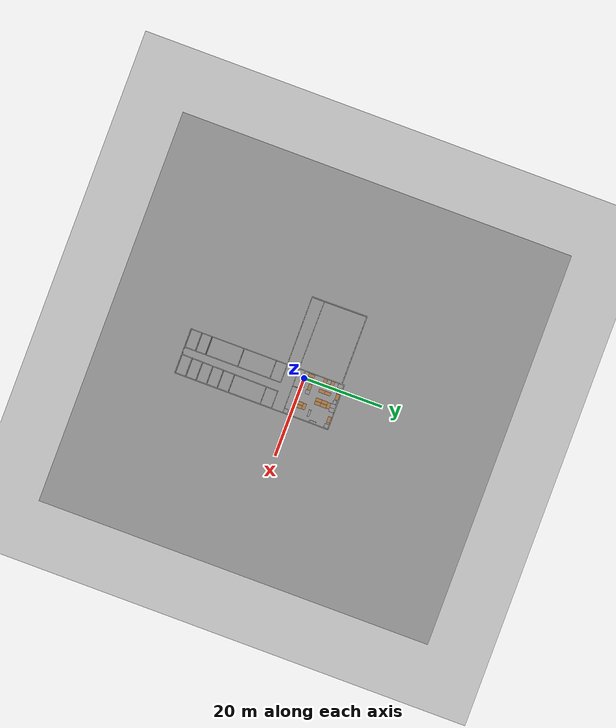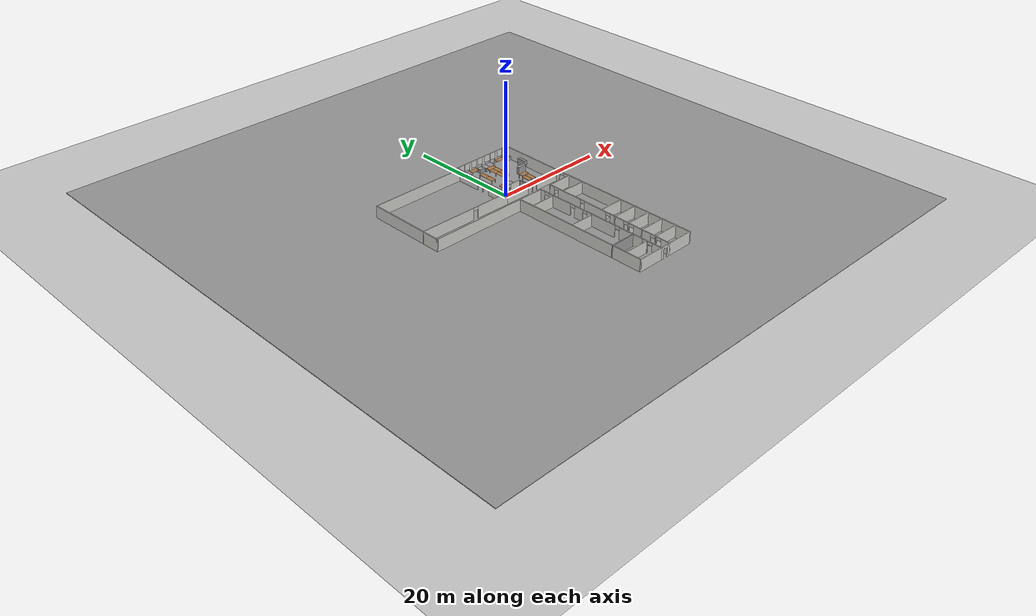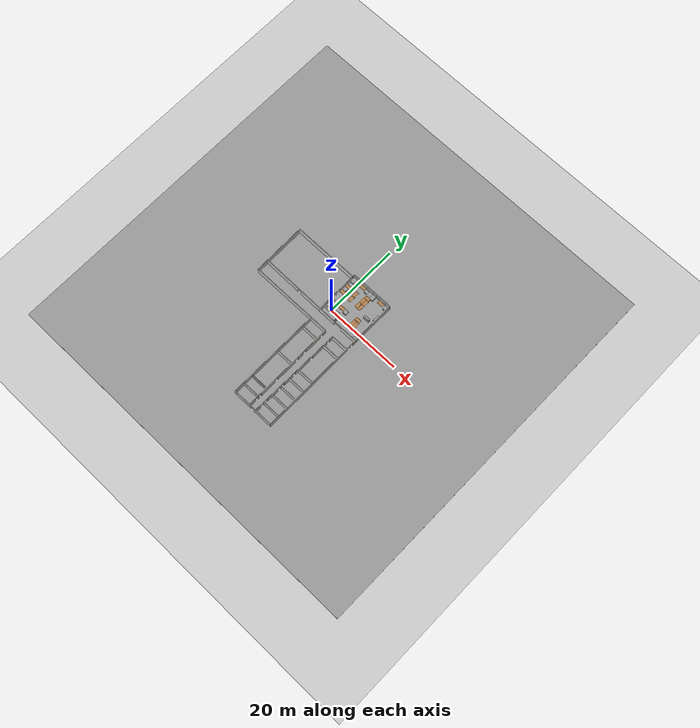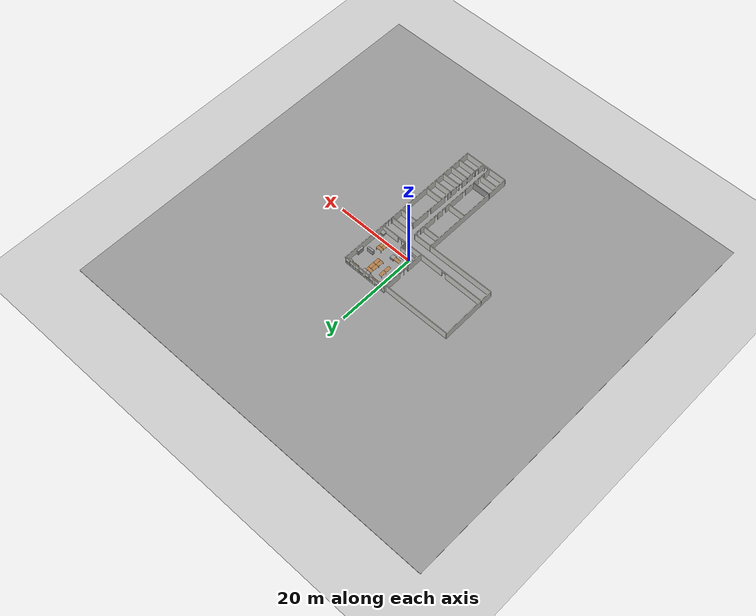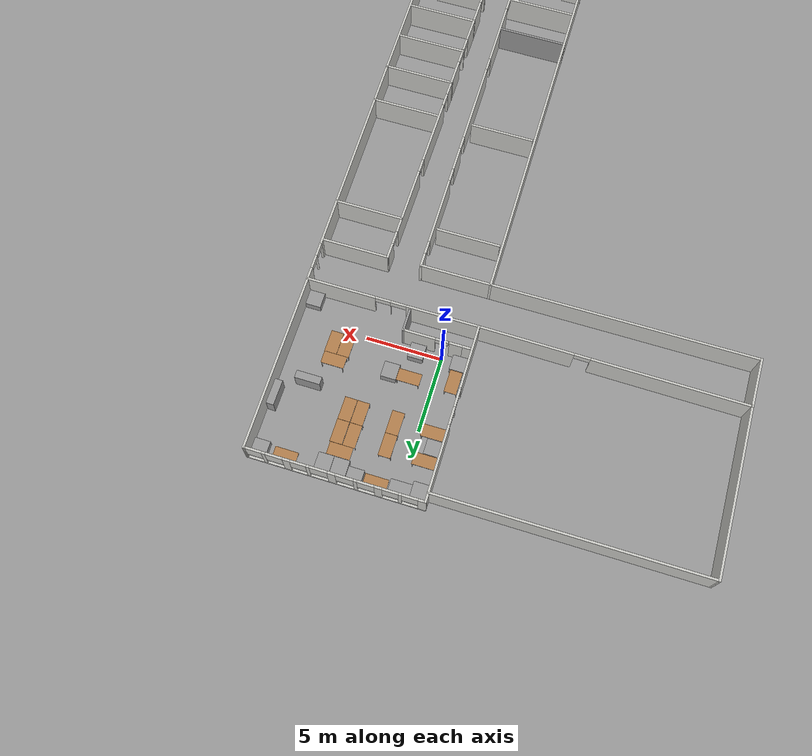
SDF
<sdf version="1.7">
 <world name="default">
  <light name="sun" type="directional">
   <pose>0 0 10 0 -0 0</pose>
   <diffuse>0.8 0.8 0.8 1</diffuse>
   <specular>0.2 0.2 0.2 1</specular>
   <attenuation>
    <range>1000</range>
    <constant>0.9</constant>
    <linear>0.01</linear>
    <quadratic>0.001</quadratic>
   </attenuation>
   <direction>-0.5 0.1 -0.9</direction>
   <spot><inner_angle>0</inner_angle><outer_angle>0</outer_angle><falloff>0</falloff></spot>
  </light>
  <model name="ground_plane">
   <static>1</static>
   <link name="link">
    <collision name="collision">
     <geometry><plane><normal>0 0 1</normal><size>100 100</size></plane></geometry>
     <surface><friction><ode><mu>100</mu><mu2>50</mu2></ode></friction></surface>
    </collision>
    <visual name="visual">
     <cast_shadows>0</cast_shadows>
     <geometry><plane><normal>0 0 1</normal><size>100 100</size></plane></geometry>
     <material>
      <script><uri>file://media/materials/scripts/gazebo.material</uri><name>Gazebo/Grey</name></script>
     </material>
    </visual>
   </link>
  </model>
  <gravity>0 0 -9.8</gravity>
  <magnetic_field>6e-06 2.3e-05 -4.2e-05</magnetic_field>
  <atmosphere type="adiabatic"/>
  <physics type="ode">
   <max_step_size>0.001</max_step_size>
   <real_time_factor>1</real_time_factor>
   <real_time_update_rate>1000</real_time_update_rate>
  </physics>
  <scene><ambient>0.4 0.4 0.4 1</ambient><background>0.7 0.7 0.7 1</background><shadows>1</shadows></scene>
  <audio><device>default</device></audio>
  <spherical_coordinates>
   <surface_model>EARTH_WGS84</surface_model>
   <latitude_deg>0</latitude_deg>
   <longitude_deg>0</longitude_deg>
   <elevation>0</elevation>
   <heading_deg>0</heading_deg>
  </spherical_coordinates>
  <model name="laboratory_features">
   <model name="Untitled5">
    <model name="LabMap">
     <link name="link_2">
      <inertial>
       <mass>1</mass>
       <inertia>
        <ixx>0.166667</ixx>
        <ixy>0</ixy>
        <ixz>0</ixz>
        <iyy>0.166667</iyy>
        <iyz>0</iyz>
        <izz>0.166667</izz>
       </inertia>
      </inertial>
      <pose>1.86689 -5.60471 0.166667 0 -0 0</pose>
      <visual name="visual">
       <geometry><box><size>1 1 1</size></box></geometry>
       <material>
        <lighting>1</lighting>
        <script><uri>file://media/materials/scripts/gazebo.material</uri><name>Gazebo/Grey</name></script>
        <shader type="pixel"/>
       </material>
      </visual>
      <collision name="collision">
       <geometry><box><size>1 1 1</size></box></geometry>
       <surface>
        <friction>
         <ode><mu>1</mu><mu2>1</mu2><fdir1>0 0 0</fdir1><slip1>0</slip1><slip2>0</slip2></ode>
         <torsional>
          <coefficient>1</coefficient>
          <patch_radius>0</patch_radius>
          <surface_radius>0</surface_radius>
          <use_patch_radius>1</use_patch_radius>
          <ode><slip>0</slip></ode>
         </torsional>
        </friction>
        <bounce><restitution_coefficient>0</restitution_coefficient><threshold>1e+06</threshold></bounce>
        <contact>
         <collide_without_contact>0</collide_without_contact>
         <collide_without_contact_bitmask>1</collide_without_contact_bitmask>
         <collide_bitmask>1</collide_bitmask>
         <ode>
          <soft_cfm>0</soft_cfm>
          <soft_erp>0.2</soft_erp>
          <kp>1e+13</kp>
          <kd>1</kd>
          <max_vel>0.01</max_vel>
          <min_depth>0</min_depth>
         </ode>
         <bullet>
          <split_impulse>1</split_impulse>
          <split_impulse_penetration_threshold>-0.01</split_impulse_penetration_threshold>
          <soft_cfm>0</soft_cfm>
          <soft_erp>0.2</soft_erp>
          <kp>1e+13</kp>
          <kd>1</kd>
         </bullet>
        </contact>
       </surface>
      </collision>
     </link>
     <link name="link_3">
      <inertial>
       <mass>1.87105</mass>
       <inertia><ixx>0.841277</ixx><ixy>0</ixy><ixz>0</ixz><iyy>1.22942</iyy><iyz>0</iyz><izz>0.4656</izz></inertia>
      </inertial>
      <pose>0.432931 -0.185022 0.166667 0 -0 0</pose>
      <visual name="visual">
       <geometry><box><size>1.65461 0.498377 2.26873</size></box></geometry>
       <material>
        <lighting>1</lighting>
        <script><uri>file://media/materials/scripts/gazebo.material</uri><name>Gazebo/Grey</name></script>
        <shader type="pixel"/>
       </material>
      </visual>
      <collision name="collision">
       <geometry><box><size>1.65461 0.498377 2.26873</size></box></geometry>
       <surface>
        <friction>
         <ode><mu>1</mu><mu2>1</mu2><fdir1>0 0 0</fdir1><slip1>0</slip1><slip2>0</slip2></ode>
         <torsional>
          <coefficient>1</coefficient>
          <patch_radius>0</patch_radius>
          <surface_radius>0</surface_radius>
          <use_patch_radius>1</use_patch_radius>
          <ode><slip>0</slip></ode>
         </torsional>
        </friction>
        <bounce><restitution_coefficient>0</restitution_coefficient><threshold>1e+06</threshold></bounce>
        <contact>
         <collide_without_contact>0</collide_without_contact>
         <collide_without_contact_bitmask>1</collide_without_contact_bitmask>
         <collide_bitmask>1</collide_bitmask>
         <ode>
          <soft_cfm>0</soft_cfm>
          <soft_erp>0.2</soft_erp>
          <kp>1e+13</kp>
          <kd>1</kd>
          <max_vel>0.01</max_vel>
          <min_depth>0</min_depth>
         </ode>
         <bullet>
          <split_impulse>1</split_impulse>
          <split_impulse_penetration_threshold>-0.01</split_impulse_penetration_threshold>
          <soft_cfm>0</soft_cfm>
          <soft_erp>0.2</soft_erp>
          <kp>1e+13</kp>
          <kd>1</kd>
         </bullet>
        </contact>
       </surface>
      </collision>
     </link>
     <link name="link_3_clone">
      <inertial>
       <mass>1.87105</mass>
       <inertia><ixx>0.841277</ixx><ixy>0</ixy><ixz>0</ixz><iyy>1.22942</iyy><iyz>0</iyz><izz>0.4656</izz></inertia>
      </inertial>
      <pose>2.12837 1.31887 0.166667 0 -0 1.55522</pose>
      <visual name="visual">
       <geometry><box><size>1.65461 0.498377 2.26873</size></box></geometry>
       <material>
        <lighting>1</lighting>
        <script><uri>file://media/materials/scripts/gazebo.material</uri><name>Gazebo/Grey</name></script>
        <shader type="pixel"/>
       </material>
      </visual>
      <collision name="collision">
       <geometry><box><size>1.65461 0.498377 2.26873</size></box></geometry>
       <surface>
        <friction>
         <ode><mu>1</mu><mu2>1</mu2><fdir1>0 0 0</fdir1><slip1>0</slip1><slip2>0</slip2></ode>
         <torsional>
          <coefficient>1</coefficient>
          <patch_radius>0</patch_radius>
          <surface_radius>0</surface_radius>
          <use_patch_radius>1</use_patch_radius>
          <ode><slip>0</slip></ode>
         </torsional>
        </friction>
        <bounce><restitution_coefficient>0</restitution_coefficient><threshold>1e+06</threshold></bounce>
        <contact>
         <collide_without_contact>0</collide_without_contact>
         <collide_without_contact_bitmask>1</collide_without_contact_bitmask>
         <collide_bitmask>1</collide_bitmask>
         <ode>
          <soft_cfm>0</soft_cfm>
          <soft_erp>0.2</soft_erp>
          <kp>1e+13</kp>
          <kd>1</kd>
          <max_vel>0.01</max_vel>
          <min_depth>0</min_depth>
         </ode>
         <bullet>
          <split_impulse>1</split_impulse>
          <split_impulse_penetration_threshold>-0.01</split_impulse_penetration_threshold>
          <soft_cfm>0</soft_cfm>
          <soft_erp>0.2</soft_erp>
          <kp>1e+13</kp>
          <kd>1</kd>
         </bullet>
        </contact>
       </surface>
      </collision>
     </link>
     <link name="link_4">
      <inertial>
       <mass>1</mass>
       <inertia>
        <ixx>0.166667</ixx>
        <ixy>0</ixy>
        <ixz>0</ixz>
        <iyy>0.166667</iyy>
        <iyz>0</iyz>
        <izz>0.166667</izz>
       </inertia>
      </inertial>
      <pose>1.88765 4.74942 0.166667 0 -0 0</pose>
      <visual name="visual">
       <geometry><box><size>1 1 1</size></box></geometry>
       <material>
        <lighting>1</lighting>
        <script><uri>file://media/materials/scripts/gazebo.material</uri><name>Gazebo/Grey</name></script>
        <shader type="pixel"/>
       </material>
      </visual>
      <collision name="collision">
       <geometry><box><size>1 1 1</size></box></geometry>
       <surface>
        <friction>
         <ode><mu>1</mu><mu2>1</mu2><fdir1>0 0 0</fdir1><slip1>0</slip1><slip2>0</slip2></ode>
         <torsional>
          <coefficient>1</coefficient>
          <patch_radius>0</patch_radius>
          <surface_radius>0</surface_radius>
          <use_patch_radius>1</use_patch_radius>
          <ode><slip>0</slip></ode>
         </torsional>
        </friction>
        <bounce><restitution_coefficient>0</restitution_coefficient><threshold>1e+06</threshold></bounce>
        <contact>
         <collide_without_contact>0</collide_without_contact>
         <collide_without_contact_bitmask>1</collide_without_contact_bitmask>
         <collide_bitmask>1</collide_bitmask>
         <ode>
          <soft_cfm>0</soft_cfm>
          <soft_erp>0.2</soft_erp>
          <kp>1e+13</kp>
          <kd>1</kd>
          <max_vel>0.01</max_vel>
          <min_depth>0</min_depth>
         </ode>
         <bullet>
          <split_impulse>1</split_impulse>
          <split_impulse_penetration_threshold>-0.01</split_impulse_penetration_threshold>
          <soft_cfm>0</soft_cfm>
          <soft_erp>0.2</soft_erp>
          <kp>1e+13</kp>
          <kd>1</kd>
         </bullet>
        </contact>
       </surface>
      </collision>
     </link>
     <model name="new_model2">
      <link name="link_0">
       <inertial>
        <mass>1</mass>
        <inertia>
         <ixx>0.166667</ixx>
         <ixy>0</ixy>
         <ixz>0</ixz>
         <iyy>0.166667</iyy>
         <iyz>0</iyz>
         <izz>0.166667</izz>
        </inertia>
       </inertial>
       <pose>-1.66046 1.09823 0.516468 0 -0 0</pose>
       <visual name="visual">
        <geometry><box><size>1 1 1</size></box></geometry>
        <material>
         <lighting>1</lighting>
         <script><uri>file://media/materials/scripts/gazebo.material</uri><name>Gazebo/Grey</name></script>
         <shader type="pixel"/>
        </material>
       </visual>
       <collision name="collision">
        <geometry><box><size>1 1 1</size></box></geometry>
        <surface>
         <friction>
          <ode><mu>1</mu><mu2>1</mu2><fdir1>0 0 0</fdir1><slip1>0</slip1><slip2>0</slip2></ode>
          <torsional>
           <coefficient>1</coefficient>
           <patch_radius>0</patch_radius>
           <surface_radius>0</surface_radius>
           <use_patch_radius>1</use_patch_radius>
           <ode><slip>0</slip></ode>
          </torsional>
         </friction>
         <bounce><restitution_coefficient>0</restitution_coefficient><threshold>1e+06</threshold></bounce>
         <contact>
          <collide_without_contact>0</collide_without_contact>
          <collide_without_contact_bitmask>1</collide_without_contact_bitmask>
          <collide_bitmask>1</collide_bitmask>
          <ode>
           <soft_cfm>0</soft_cfm>
           <soft_erp>0.2</soft_erp>
           <kp>1e+13</kp>
           <kd>1</kd>
           <max_vel>0.01</max_vel>
           <min_depth>0</min_depth>
          </ode>
          <bullet>
           <split_impulse>1</split_impulse>
           <split_impulse_penetration_threshold>-0.01</split_impulse_penetration_threshold>
           <soft_cfm>0</soft_cfm>
           <soft_erp>0.2</soft_erp>
           <kp>1e+13</kp>
           <kd>1</kd>
          </bullet>
         </contact>
        </surface>
       </collision>
      </link>
      <link name="link_1">
       <inertial>
        <mass>1</mass>
        <inertia>
         <ixx>0.166667</ixx>
         <ixy>0</ixy>
         <ixz>0</ixz>
         <iyy>0.166667</iyy>
         <iyz>0</iyz>
         <izz>0.166667</izz>
        </inertia>
       </inertial>
       <pose>1.10369 1.04984 0.516468 0 -0 0</pose>
       <visual name="visual">
        <geometry><box><size>1 1 1</size></box></geometry>
        <material>
         <lighting>1</lighting>
         <script><uri>file://media/materials/scripts/gazebo.material</uri><name>Gazebo/Grey</name></script>
         <shader type="pixel"/>
        </material>
       </visual>
       <collision name="collision">
        <geometry><box><size>1 1 1</size></box></geometry>
        <surface>
         <friction>
          <ode><mu>1</mu><mu2>1</mu2><fdir1>0 0 0</fdir1><slip1>0</slip1><slip2>0</slip2></ode>
          <torsional>
           <coefficient>1</coefficient>
           <patch_radius>0</patch_radius>
           <surface_radius>0</surface_radius>
           <use_patch_radius>1</use_patch_radius>
           <ode><slip>0</slip></ode>
          </torsional>
         </friction>
         <bounce><restitution_coefficient>0</restitution_coefficient><threshold>1e+06</threshold></bounce>
         <contact>
          <collide_without_contact>0</collide_without_contact>
          <collide_without_contact_bitmask>1</collide_without_contact_bitmask>
          <collide_bitmask>1</collide_bitmask>
          <ode>
           <soft_cfm>0</soft_cfm>
           <soft_erp>0.2</soft_erp>
           <kp>1e+13</kp>
           <kd>1</kd>
           <max_vel>0.01</max_vel>
           <min_depth>0</min_depth>
          </ode>
          <bullet>
           <split_impulse>1</split_impulse>
           <split_impulse_penetration_threshold>-0.01</split_impulse_penetration_threshold>
           <soft_cfm>0</soft_cfm>
           <soft_erp>0.2</soft_erp>
           <kp>1e+13</kp>
           <kd>1</kd>
          </bullet>
         </contact>
        </surface>
       </collision>
      </link>
      <link name="link_2">
       <inertial>
        <mass>1.03239</mass>
        <inertia>
         <ixx>0.177727</ixx>
         <ixy>0</ixy>
         <ixz>0</ixz>
         <iyy>0.172064</iyy>
         <iyz>0</iyz>
         <izz>0.177727</izz>
        </inertia>
       </inertial>
       <pose>2.33011 2.7769 0.516468 0 -0 0</pose>
       <visual name="visual">
        <geometry><box><size>1 1.03239 1</size></box></geometry>
        <material>
         <lighting>1</lighting>
         <script><uri>file://media/materials/scripts/gazebo.material</uri><name>Gazebo/Grey</name></script>
         <shader type="pixel"/>
        </material>
       </visual>
       <collision name="collision">
        <geometry><box><size>1 1.03239 1</size></box></geometry>
        <surface>
         <friction>
          <ode><mu>1</mu><mu2>1</mu2><fdir1>0 0 0</fdir1><slip1>0</slip1><slip2>0</slip2></ode>
          <torsional>
           <coefficient>1</coefficient>
           <patch_radius>0</patch_radius>
           <surface_radius>0</surface_radius>
           <use_patch_radius>1</use_patch_radius>
           <ode><slip>0</slip></ode>
          </torsional>
         </friction>
         <bounce><restitution_coefficient>0</restitution_coefficient><threshold>1e+06</threshold></bounce>
         <contact>
          <collide_without_contact>0</collide_without_contact>
          <collide_without_contact_bitmask>1</collide_without_contact_bitmask>
          <collide_bitmask>1</collide_bitmask>
          <ode>
           <soft_cfm>0</soft_cfm>
           <soft_erp>0.2</soft_erp>
           <kp>1e+13</kp>
           <kd>1</kd>
           <max_vel>0.01</max_vel>
           <min_depth>0</min_depth>
          </ode>
          <bullet>
           <split_impulse>1</split_impulse>
           <split_impulse_penetration_threshold>-0.01</split_impulse_penetration_threshold>
           <soft_cfm>0</soft_cfm>
           <soft_erp>0.2</soft_erp>
           <kp>1e+13</kp>
           <kd>1</kd>
          </bullet>
         </contact>
        </surface>
       </collision>
      </link>
      <link name="link_3">
       <inertial>
        <mass>1</mass>
        <inertia>
         <ixx>0.166667</ixx>
         <ixy>0</ixy>
         <ixz>0</ixz>
         <iyy>0.166667</iyy>
         <iyz>0</iyz>
         <izz>0.166667</izz>
        </inertia>
       </inertial>
       <pose>-1.68316 6.81972 0.516468 0 -0 0</pose>
       <visual name="visual">
        <geometry><box><size>1 1 1</size></box></geometry>
        <material>
         <lighting>1</lighting>
         <script><uri>file://media/materials/scripts/gazebo.material</uri><name>Gazebo/Grey</name></script>
         <shader type="pixel"/>
        </material>
       </visual>
       <collision name="collision">
        <geometry><box><size>1 1 1</size></box></geometry>
        <surface>
         <friction>
          <ode><mu>1</mu><mu2>1</mu2><fdir1>0 0 0</fdir1><slip1>0</slip1><slip2>0</slip2></ode>
          <torsional>
           <coefficient>1</coefficient>
           <patch_radius>0</patch_radius>
           <surface_radius>0</surface_radius>
           <use_patch_radius>1</use_patch_radius>
           <ode><slip>0</slip></ode>
          </torsional>
         </friction>
         <bounce><restitution_coefficient>0</restitution_coefficient><threshold>1e+06</threshold></bounce>
         <contact>
          <collide_without_contact>0</collide_without_contact>
          <collide_without_contact_bitmask>1</collide_without_contact_bitmask>
          <collide_bitmask>1</collide_bitmask>
          <ode>
           <soft_cfm>0</soft_cfm>
           <soft_erp>0.2</soft_erp>
           <kp>1e+13</kp>
           <kd>1</kd>
           <max_vel>0.01</max_vel>
           <min_depth>0</min_depth>
          </ode>
          <bullet>
           <split_impulse>1</split_impulse>
           <split_impulse_penetration_threshold>-0.01</split_impulse_penetration_threshold>
           <soft_cfm>0</soft_cfm>
           <soft_erp>0.2</soft_erp>
           <kp>1e+13</kp>
           <kd>1</kd>
          </bullet>
         </contact>
        </surface>
       </collision>
      </link>
      <link name="link_4">
       <inertial>
        <mass>1.28316</mass>
        <inertia>
         <ixx>0.282993</ixx>
         <ixy>0</ixy>
         <ixz>0</ixz>
         <iyy>0.213861</iyy>
         <iyz>0</iyz>
         <izz>0.282993</izz>
        </inertia>
       </inertial>
       <pose>-1.65758 9.75819 0.516468 0 -0 0</pose>
       <visual name="visual">
        <geometry><box><size>1 1.28317 1</size></box></geometry>
        <material>
         <lighting>1</lighting>
         <script><uri>file://media/materials/scripts/gazebo.material</uri><name>Gazebo/Grey</name></script>
         <shader type="pixel"/>
        </material>
       </visual>
       <collision name="collision">
        <geometry><box><size>1 1.28317 1</size></box></geometry>
        <surface>
         <friction>
          <ode><mu>1</mu><mu2>1</mu2><fdir1>0 0 0</fdir1><slip1>0</slip1><slip2>0</slip2></ode>
          <torsional>
           <coefficient>1</coefficient>
           <patch_radius>0</patch_radius>
           <surface_radius>0</surface_radius>
           <use_patch_radius>1</use_patch_radius>
           <ode><slip>0</slip></ode>
          </torsional>
         </friction>
         <bounce><restitution_coefficient>0</restitution_coefficient><threshold>1e+06</threshold></bounce>
         <contact>
          <collide_without_contact>0</collide_without_contact>
          <collide_without_contact_bitmask>1</collide_without_contact_bitmask>
          <collide_bitmask>1</collide_bitmask>
          <ode>
           <soft_cfm>0</soft_cfm>
           <soft_erp>0.2</soft_erp>
           <kp>1e+13</kp>
           <kd>1</kd>
           <max_vel>0.01</max_vel>
           <min_depth>0</min_depth>
          </ode>
          <bullet>
           <split_impulse>1</split_impulse>
           <split_impulse_penetration_threshold>-0.01</split_impulse_penetration_threshold>
           <soft_cfm>0</soft_cfm>
           <soft_erp>0.2</soft_erp>
           <kp>1e+13</kp>
           <kd>1</kd>
          </bullet>
         </contact>
        </surface>
       </collision>
      </link>
      <link name="link_5">
       <inertial>
        <mass>1.37081</mass>
        <inertia>
         <ixx>0.228469</ixx>
         <ixy>0</ixy>
         <ixz>0</ixz>
         <iyy>0.328897</iyy>
         <iyz>0</iyz>
         <izz>0.328897</izz>
        </inertia>
       </inertial>
       <pose>-0.475085 9.87452 0.516468 0 -0 0</pose>
       <visual name="visual">
        <geometry><box><size>1.37082 1 1</size></box></geometry>
        <material>
         <lighting>1</lighting>
         <script><uri>file://media/materials/scripts/gazebo.material</uri><name>Gazebo/Grey</name></script>
         <shader type="pixel"/>
        </material>
       </visual>
       <collision name="collision">
        <geometry><box><size>1.37082 1 1</size></box></geometry>
        <surface>
         <friction>
          <ode><mu>1</mu><mu2>1</mu2><fdir1>0 0 0</fdir1><slip1>0</slip1><slip2>0</slip2></ode>
          <torsional>
           <coefficient>1</coefficient>
           <patch_radius>0</patch_radius>
           <surface_radius>0</surface_radius>
           <use_patch_radius>1</use_patch_radius>
           <ode><slip>0</slip></ode>
          </torsional>
         </friction>
         <bounce><restitution_coefficient>0</restitution_coefficient><threshold>1e+06</threshold></bounce>
         <contact>
          <collide_without_contact>0</collide_without_contact>
          <collide_without_contact_bitmask>1</collide_without_contact_bitmask>
          <collide_bitmask>1</collide_bitmask>
          <ode>
           <soft_cfm>0</soft_cfm>
           <soft_erp>0.2</soft_erp>
           <kp>1e+13</kp>
           <kd>1</kd>
           <max_vel>0.01</max_vel>
           <min_depth>0</min_depth>
          </ode>
          <bullet>
           <split_impulse>1</split_impulse>
           <split_impulse_penetration_threshold>-0.01</split_impulse_penetration_threshold>
           <soft_cfm>0</soft_cfm>
           <soft_erp>0.2</soft_erp>
           <kp>1e+13</kp>
           <kd>1</kd>
          </bullet>
         </contact>
        </surface>
       </collision>
      </link>
      <link name="link_7">
       <inertial>
        <mass>0.793101</mass>
        <inertia>
         <ixx>0.107664</ixx>
         <ixy>0</ixy>
         <ixz>0</ixz>
         <iyy>0.132183</iyy>
         <iyz>0</iyz>
         <izz>0.107664</izz>
        </inertia>
       </inertial>
       <pose>2.37708 9.78834 0.516468 0 -0 0</pose>
       <visual name="visual">
        <geometry><box><size>1 0.7931 1</size></box></geometry>
        <material>
         <lighting>1</lighting>
         <script><uri>file://media/materials/scripts/gazebo.material</uri><name>Gazebo/Grey</name></script>
         <shader type="pixel"/>
        </material>
       </visual>
       <collision name="collision">
        <geometry><box><size>1 0.7931 1</size></box></geometry>
        <surface>
         <friction>
          <ode><mu>1</mu><mu2>1</mu2><fdir1>0 0 0</fdir1><slip1>0</slip1><slip2>0</slip2></ode>
          <torsional>
           <coefficient>1</coefficient>
           <patch_radius>0</patch_radius>
           <surface_radius>0</surface_radius>
           <use_patch_radius>1</use_patch_radius>
           <ode><slip>0</slip></ode>
          </torsional>
         </friction>
         <bounce><restitution_coefficient>0</restitution_coefficient><threshold>1e+06</threshold></bounce>
         <contact>
          <collide_without_contact>0</collide_without_contact>
          <collide_without_contact_bitmask>1</collide_without_contact_bitmask>
          <collide_bitmask>1</collide_bitmask>
          <ode>
           <soft_cfm>0</soft_cfm>
           <soft_erp>0.2</soft_erp>
           <kp>1e+13</kp>
           <kd>1</kd>
           <max_vel>0.01</max_vel>
           <min_depth>0</min_depth>
          </ode>
          <bullet>
           <split_impulse>1</split_impulse>
           <split_impulse_penetration_threshold>-0.01</split_impulse_penetration_threshold>
           <soft_cfm>0</soft_cfm>
           <soft_erp>0.2</soft_erp>
           <kp>1e+13</kp>
           <kd>1</kd>
          </bullet>
         </contact>
        </surface>
       </collision>
      </link>
      <link name="link_8">
       <inertial>
        <mass>1.31027</mass>
        <inertia>
         <ixx>0.296645</ixx>
         <ixy>0</ixy>
         <ixz>0</ixz>
         <iyy>0.218378</iyy>
         <iyz>0</iyz>
         <izz>0.296645</izz>
        </inertia>
       </inertial>
       <pose>3.40898 9.72838 0.516468 0 -0 0</pose>
       <visual name="visual">
        <geometry><box><size>1 1.31027 1</size></box></geometry>
        <material>
         <lighting>1</lighting>
         <script><uri>file://media/materials/scripts/gazebo.material</uri><name>Gazebo/Grey</name></script>
         <shader type="pixel"/>
        </material>
       </visual>
       <collision name="collision">
        <geometry><box><size>1 1.31027 1</size></box></geometry>
        <surface>
         <friction>
          <ode><mu>1</mu><mu2>1</mu2><fdir1>0 0 0</fdir1><slip1>0</slip1><slip2>0</slip2></ode>
          <torsional>
           <coefficient>1</coefficient>
           <patch_radius>0</patch_radius>
           <surface_radius>0</surface_radius>
           <use_patch_radius>1</use_patch_radius>
           <ode><slip>0</slip></ode>
          </torsional>
         </friction>
         <bounce><restitution_coefficient>0</restitution_coefficient><threshold>1e+06</threshold></bounce>
         <contact>
          <collide_without_contact>0</collide_without_contact>
          <collide_without_contact_bitmask>1</collide_without_contact_bitmask>
          <collide_bitmask>1</collide_bitmask>
          <ode>
           <soft_cfm>0</soft_cfm>
           <soft_erp>0.2</soft_erp>
           <kp>1e+13</kp>
           <kd>1</kd>
           <max_vel>0.01</max_vel>
           <min_depth>0</min_depth>
          </ode>
          <bullet>
           <split_impulse>1</split_impulse>
           <split_impulse_penetration_threshold>-0.01</split_impulse_penetration_threshold>
           <soft_cfm>0</soft_cfm>
           <soft_erp>0.2</soft_erp>
           <kp>1e+13</kp>
           <kd>1</kd>
          </bullet>
         </contact>
        </surface>
       </collision>
      </link>
      <link name="link_9">
       <inertial>
        <mass>1.28236</mass>
        <inertia>
         <ixx>0.282593</ixx>
         <ixy>0</ixy>
         <ixz>0</ixz>
         <iyy>0.213727</iyy>
         <iyz>0</iyz>
         <izz>0.282593</izz>
        </inertia>
       </inertial>
       <pose>4.41567 9.70967 0.516468 0 -0 0</pose>
       <visual name="visual">
        <geometry><box><size>1 1.28235 1</size></box></geometry>
        <material>
         <lighting>1</lighting>
         <script><uri>file://media/materials/scripts/gazebo.material</uri><name>Gazebo/Grey</name></script>
         <shader type="pixel"/>
        </material>
       </visual>
       <collision name="collision">
        <geometry><box><size>1 1.28235 1</size></box></geometry>
        <surface>
         <friction>
          <ode><mu>1</mu><mu2>1</mu2><fdir1>0 0 0</fdir1><slip1>0</slip1><slip2>0</slip2></ode>
          <torsional>
           <coefficient>1</coefficient>
           <patch_radius>0</patch_radius>
           <surface_radius>0</surface_radius>
           <use_patch_radius>1</use_patch_radius>
           <ode><slip>0</slip></ode>
          </torsional>
         </friction>
         <bounce><restitution_coefficient>0</restitution_coefficient><threshold>1e+06</threshold></bounce>
         <contact>
          <collide_without_contact>0</collide_without_contact>
          <collide_without_contact_bitmask>1</collide_without_contact_bitmask>
          <collide_bitmask>1</collide_bitmask>
          <ode>
           <soft_cfm>0</soft_cfm>
           <soft_erp>0.2</soft_erp>
           <kp>1e+13</kp>
           <kd>1</kd>
           <max_vel>0.01</max_vel>
           <min_depth>0</min_depth>
          </ode>
          <bullet>
           <split_impulse>1</split_impulse>
           <split_impulse_penetration_threshold>-0.01</split_impulse_penetration_threshold>
           <soft_cfm>0</soft_cfm>
           <soft_erp>0.2</soft_erp>
           <kp>1e+13</kp>
           <kd>1</kd>
          </bullet>
         </contact>
        </surface>
       </collision>
      </link>
      <model name="LabModel">
       <pose>-5.26511 -9.10909 0.016468 0 -0 0</pose>
       <link name="Wall_1">
        <collision name="Wall_1_Collision">
         <geometry><box><size>11.7388 0.15 2.5</size></box></geometry>
         <pose>0 0 1.25 0 -0 0</pose>
        </collision>
        <visual name="Wall_1_Visual">
         <pose>0 0 1.25 0 -0 0</pose>
         <geometry><box><size>11.7388 0.15 2.5</size></box></geometry>
         <material>
          <script><uri>file://media/materials/scripts/gazebo.material</uri><name>Gazebo/CeilingTiled</name></script>
          <ambient>1 1 1 1</ambient>
         </material>
         <meta><layer>0</layer></meta>
        </visual>
        <pose>14.3214 13.8027 0 0 -0 1.56589</pose>
       </link>
       <link name="Wall_113">
        <collision name="Wall_113_Collision">
         <geometry><box><size>3.30454 0.15 2.5</size></box></geometry>
         <pose>0 0 1.25 0 -0 0</pose>
        </collision>
        <visual name="Wall_113_Visual">
         <pose>0 0 1.25 0 -0 0</pose>
         <geometry><box><size>3.30454 0.15 2.5</size></box></geometry>
         <material>
          <script><uri>file://media/materials/scripts/gazebo.material</uri><name>Gazebo/CeilingTiled</name></script>
          <ambient>1 1 1 1</ambient>
         </material>
         <meta><layer>0</layer></meta>
        </visual>
        <pose>-14.2575 6.56747 0 0 -0 -1.57202</pose>
       </link>
       <link name="Wall_16">
        <collision name="Wall_16_Collision">
         <geometry><box><size>11.0154 0.15 2.5</size></box></geometry>
         <pose>0 0 1.25 0 -0 0</pose>
        </collision>
        <visual name="Wall_16_Visual">
         <pose>0 0 1.25 0 -0 0</pose>
         <geometry><box><size>11.0154 0.15 2.5</size></box></geometry>
         <material>
          <script><uri>file://media/materials/scripts/gazebo.material</uri><name>Gazebo/CeilingTiled</name></script>
          <ambient>1 1 1 1</ambient>
         </material>
         <meta><layer>0</layer></meta>
        </visual>
        <pose>-14.3026 13.5773 0 0 -0 1.57945</pose>
       </link>
       <link name="Wall_17">
        <collision name="Wall_17_Collision">
         <geometry><box><size>17.5 0.15 2.5</size></box></geometry>
         <pose>0 0 1.25 0 -0 0</pose>
        </collision>
        <visual name="Wall_17_Visual">
         <pose>0 0 1.25 0 -0 0</pose>
         <geometry><box><size>17.5 0.15 2.5</size></box></geometry>
         <material>
          <script><uri>file://media/materials/scripts/gazebo.material</uri><name>Gazebo/CeilingTiled</name></script>
          <ambient>1 1 1 1</ambient>
         </material>
         <meta><layer>0</layer></meta>
        </visual>
        <pose>-5.67083 19.0098 0 0 -0 0</pose>
       </link>
       <link name="Wall_19">
        <collision name="Wall_19_Collision">
         <geometry><box><size>4.5 0.15 2.5</size></box></geometry>
         <pose>0 0 1.25 0 -0 0</pose>
        </collision>
        <visual name="Wall_19_Visual">
         <pose>0 0 1.25 0 -0 0</pose>
         <geometry><box><size>4.5 0.15 2.5</size></box></geometry>
         <material>
          <script><uri>file://media/materials/scripts/gazebo.material</uri><name>Gazebo/CeilingTiled</name></script>
          <ambient>1 1 1 1</ambient>
         </material>
         <meta><layer>0</layer></meta>
        </visual>
        <pose>12.0644 5.08895 0 0 -0 3.14159</pose>
       </link>
       <link name="Wall_20">
        <pose>9.71758 -7.24949 0 0 -0 -1.58472</pose>
        <visual name="Wall_20_Visual_0">
         <pose>-11.8689 0 1.25 0 -0 0</pose>
         <geometry><box><size>1.09097 0.15 2.5</size></box></geometry>
         <material>
          <script><uri>file://media/materials/scripts/gazebo.material</uri><name>Gazebo/CeilingTiled</name></script>
          <ambient>1 1 1 1</ambient>
         </material>
         <meta><layer>0</layer></meta>
        </visual>
        <collision name="Wall_20_Collision_0">
         <geometry><box><size>1.09097 0.15 2.5</size></box></geometry>
         <pose>-11.8689 0 1.25 0 -0 0</pose>
        </collision>
        <visual name="Wall_20_Visual_1">
         <pose>-8.07474 0 1.25 0 -0 0</pose>
         <geometry><box><size>4.69725 0.15 2.5</size></box></geometry>
         <material>
          <script><uri>file://media/materials/scripts/gazebo.material</uri><name>Gazebo/CeilingTiled</name></script>
          <ambient>1 1 1 1</ambient>
         </material>
         <meta><layer>0</layer></meta>
        </visual>
        <collision name="Wall_20_Collision_1">
         <geometry><box><size>4.69725 0.15 2.5</size></box></geometry>
         <pose>-8.07474 0 1.25 0 -0 0</pose>
        </collision>
        <visual name="Wall_20_Visual_2">
         <pose>-2.55992 0 1.25 0 -0 0</pose>
         <geometry><box><size>4.53239 0.15 2.5</size></box></geometry>
         <material>
          <script><uri>file://media/materials/scripts/gazebo.material</uri><name>Gazebo/CeilingTiled</name></script>
          <ambient>1 1 1 1</ambient>
         </material>
         <meta><layer>0</layer></meta>
        </visual>
        <collision name="Wall_20_Collision_2">
         <geometry><box><size>4.53239 0.15 2.5</size></box></geometry>
         <pose>-2.55992 0 1.25 0 -0 0</pose>
        </collision>
        <visual name="Wall_20_Visual_3">
         <pose>1.99995 0 1.25 0 -0 0</pose>
         <geometry><box><size>2.78735 0.15 2.5</size></box></geometry>
         <material>
          <script><uri>file://media/materials/scripts/gazebo.material</uri><name>Gazebo/CeilingTiled</name></script>
          <ambient>1 1 1 1</ambient>
         </material>
         <meta><layer>0</layer></meta>
        </visual>
        <collision name="Wall_20_Collision_3">
         <geometry><box><size>2.78735 0.15 2.5</size></box></geometry>
         <pose>1.99995 0 1.25 0 -0 0</pose>
        </collision>
        <visual name="Wall_20_Visual_4">
         <pose>4.37423 0 1.25 0 -0 0</pose>
         <geometry><box><size>0.161222 0.15 2.5</size></box></geometry>
         <material>
          <script><uri>file://media/materials/scripts/gazebo.material</uri><name>Gazebo/CeilingTiled</name></script>
          <ambient>1 1 1 1</ambient>
         </material>
         <meta><layer>0</layer></meta>
        </visual>
        <collision name="Wall_20_Collision_4">
         <geometry><box><size>0.161222 0.15 2.5</size></box></geometry>
         <pose>4.37423 0 1.25 0 -0 0</pose>
        </collision>
        <visual name="Wall_20_Visual_5">
         <pose>7.01378 0 1.25 0 -0 0</pose>
         <geometry><box><size>3.31787 0.15 2.5</size></box></geometry>
         <material>
          <script><uri>file://media/materials/scripts/gazebo.material</uri><name>Gazebo/CeilingTiled</name></script>
          <ambient>1 1 1 1</ambient>
         </material>
         <meta><layer>0</layer></meta>
        </visual>
        <collision name="Wall_20_Collision_5">
         <geometry><box><size>3.31787 0.15 2.5</size></box></geometry>
         <pose>7.01378 0 1.25 0 -0 0</pose>
        </collision>
        <visual name="Wall_20_Visual_6">
         <pose>9.70622 0 1.25 0 -0 0</pose>
         <geometry><box><size>0.267002 0.15 2.5</size></box></geometry>
         <material>
          <script><uri>file://media/materials/scripts/gazebo.material</uri><name>Gazebo/CeilingTiled</name></script>
          <ambient>1 1 1 1</ambient>
         </material>
         <meta><layer>0</layer></meta>
        </visual>
        <collision name="Wall_20_Collision_6">
         <geometry><box><size>0.267002 0.15 2.5</size></box></geometry>
         <pose>9.70622 0 1.25 0 -0 0</pose>
        </collision>
        <visual name="Wall_20_Visual_7">
         <pose>11.577 0 1.25 0 -0 0</pose>
         <geometry><box><size>1.67461 0.15 2.5</size></box></geometry>
         <material>
          <script><uri>file://media/materials/scripts/gazebo.material</uri><name>Gazebo/CeilingTiled</name></script>
          <ambient>1 1 1 1</ambient>
         </material>
         <meta><layer>0</layer></meta>
        </visual>
        <collision name="Wall_20_Collision_7">
         <geometry><box><size>1.67461 0.15 2.5</size></box></geometry>
         <pose>11.577 0 1.25 0 -0 0</pose>
        </collision>
        <visual name="Wall_20_Visual_8">
         <pose>-10.8734 0 2.25 0 -0 0</pose>
         <geometry><box><size>0.9 0.15 0.5</size></box></geometry>
         <material>
          <script><uri>file://media/materials/scripts/gazebo.material</uri><name>Gazebo/CeilingTiled</name></script>
          <ambient>1 1 1 1</ambient>
         </material>
         <meta><layer>0</layer></meta>
        </visual>
        <collision name="Wall_20_Collision_8">
         <geometry><box><size>0.9 0.15 0.5</size></box></geometry>
         <pose>-10.8734 0 2.25 0 -0 0</pose>
        </collision>
        <visual name="Wall_20_Visual_9">
         <pose>-5.27611 0 2.25 0 -0 0</pose>
         <geometry><box><size>0.9 0.15 0.5</size></box></geometry>
         <material>
          <script><uri>file://media/materials/scripts/gazebo.material</uri><name>Gazebo/CeilingTiled</name></script>
          <ambient>1 1 1 1</ambient>
         </material>
         <meta><layer>0</layer></meta>
        </visual>
        <collision name="Wall_20_Collision_9">
         <geometry><box><size>0.9 0.15 0.5</size></box></geometry>
         <pose>-5.27611 0 2.25 0 -0 0</pose>
        </collision>
        <visual name="Wall_20_Visual_10">
         <pose>0.156279 0 2.25 0 -0 0</pose>
         <geometry><box><size>0.9 0.15 0.5</size></box></geometry>
         <material>
          <script><uri>file://media/materials/scripts/gazebo.material</uri><name>Gazebo/CeilingTiled</name></script>
          <ambient>1 1 1 1</ambient>
         </material>
         <meta><layer>0</layer></meta>
        </visual>
        <collision name="Wall_20_Collision_10">
         <geometry><box><size>0.9 0.15 0.5</size></box></geometry>
         <pose>0.156279 0 2.25 0 -0 0</pose>
        </collision>
        <visual name="Wall_20_Visual_11">
         <pose>3.84362 0 2.25 0 -0 0</pose>
         <geometry><box><size>0.9 0.15 0.5</size></box></geometry>
         <material>
          <script><uri>file://media/materials/scripts/gazebo.material</uri><name>Gazebo/CeilingTiled</name></script>
          <ambient>1 1 1 1</ambient>
         </material>
         <meta><layer>0</layer></meta>
        </visual>
        <collision name="Wall_20_Collision_11">
         <geometry><box><size>0.9 0.15 0.5</size></box></geometry>
         <pose>3.84362 0 2.25 0 -0 0</pose>
        </collision>
        <visual name="Wall_20_Visual_12">
         <pose>4.90484 0 2.25 0 -0 0</pose>
         <geometry><box><size>0.9 0.15 0.5</size></box></geometry>
         <material>
          <script><uri>file://media/materials/scripts/gazebo.material</uri><name>Gazebo/CeilingTiled</name></script>
          <ambient>1 1 1 1</ambient>
         </material>
         <meta><layer>0</layer></meta>
        </visual>
        <collision name="Wall_20_Collision_12">
         <geometry><box><size>0.9 0.15 0.5</size></box></geometry>
         <pose>4.90484 0 2.25 0 -0 0</pose>
        </collision>
        <visual name="Wall_20_Visual_13">
         <pose>9.12272 0 2.25 0 -0 0</pose>
         <geometry><box><size>0.9 0.15 0.5</size></box></geometry>
         <material>
          <script><uri>file://media/materials/scripts/gazebo.material</uri><name>Gazebo/CeilingTiled</name></script>
          <ambient>1 1 1 1</ambient>
         </material>
         <meta><layer>0</layer></meta>
        </visual>
        <collision name="Wall_20_Collision_13">
         <geometry><box><size>0.9 0.15 0.5</size></box></geometry>
         <pose>9.12272 0 2.25 0 -0 0</pose>
        </collision>
        <visual name="Wall_20_Visual_14">
         <pose>10.2897 0 2.25 0 -0 0</pose>
         <geometry><box><size>0.9 0.15 0.5</size></box></geometry>
         <material>
          <script><uri>file://media/materials/scripts/gazebo.material</uri><name>Gazebo/CeilingTiled</name></script>
          <ambient>1 1 1 1</ambient>
         </material>
         <meta><layer>0</layer></meta>
        </visual>
        <collision name="Wall_20_Collision_14">
         <geometry><box><size>0.9 0.15 0.5</size></box></geometry>
         <pose>10.2897 0 2.25 0 -0 0</pose>
        </collision>
       </link>
       <link name="Wall_21">
        <collision name="Wall_21_Collision">
         <geometry><box><size>4.75 0.15 2.5</size></box></geometry>
         <pose>0 0 1.25 0 -0 0</pose>
        </collision>
        <visual name="Wall_21_Visual">
         <pose>0 0 1.25 0 -0 0</pose>
         <geometry><box><size>4.75 0.15 2.5</size></box></geometry>
         <material>
          <script><uri>file://media/materials/scripts/gazebo.material</uri><name>Gazebo/CeilingTiled</name></script>
          <ambient>1 1 1 1</ambient>
         </material>
         <meta><layer>0</layer></meta>
        </visual>
        <pose>11.8687 -19.5879 0 0 -0 0</pose>
       </link>
       <link name="Wall_23">
        <pose>14.2987 -5.79734 0 0 -0 -1.5708</pose>
        <visual name="Wall_23_Visual_0">
         <pose>-13.4441 0 1.25 0 -0 0</pose>
         <geometry><box><size>0.861844 0.15 2.5</size></box></geometry>
         <material>
          <script><uri>file://media/materials/scripts/gazebo.material</uri><name>Gazebo/CeilingTiled</name></script>
          <ambient>1 1 1 1</ambient>
         </material>
         <meta><layer>0</layer></meta>
        </visual>
        <collision name="Wall_23_Collision_0">
         <geometry><box><size>0.861844 0.15 2.5</size></box></geometry>
         <pose>-13.4441 0 1.25 0 -0 0</pose>
        </collision>
        <visual name="Wall_23_Visual_1">
         <pose>-12.1111 0 1.25 0 -0 0</pose>
         <geometry><box><size>0.004186 0.15 2.5</size></box></geometry>
         <material>
          <script><uri>file://media/materials/scripts/gazebo.material</uri><name>Gazebo/CeilingTiled</name></script>
          <ambient>1 1 1 1</ambient>
         </material>
         <meta><layer>0</layer></meta>
        </visual>
        <collision name="Wall_23_Collision_1">
         <geometry><box><size>0.004186 0.15 2.5</size></box></geometry>
         <pose>-12.1111 0 1.25 0 -0 0</pose>
        </collision>
        <visual name="Wall_23_Visual_2">
         <pose>1.33302 0 1.25 0 -0 0</pose>
         <geometry><box><size>25.084 0.15 2.5</size></box></geometry>
         <material>
          <script><uri>file://media/materials/scripts/gazebo.material</uri><name>Gazebo/CeilingTiled</name></script>
          <ambient>1 1 1 1</ambient>
         </material>
         <meta><layer>0</layer></meta>
        </visual>
        <collision name="Wall_23_Collision_2">
         <geometry><box><size>25.084 0.15 2.5</size></box></geometry>
         <pose>1.33302 0 1.25 0 -0 0</pose>
        </collision>
        <visual name="Wall_23_Visual_3">
         <pose>-12.5632 0 2.25 0 -0 0</pose>
         <geometry><box><size>0.9 0.15 0.5</size></box></geometry>
         <material>
          <script><uri>file://media/materials/scripts/gazebo.material</uri><name>Gazebo/CeilingTiled</name></script>
          <ambient>1 1 1 1</ambient>
         </material>
         <meta><layer>0</layer></meta>
        </visual>
        <collision name="Wall_23_Collision_3">
         <geometry><box><size>0.9 0.15 0.5</size></box></geometry>
         <pose>-12.5632 0 2.25 0 -0 0</pose>
        </collision>
        <visual name="Wall_23_Visual_4">
         <pose>-11.659 0 2.25 0 -0 0</pose>
         <geometry><box><size>0.9 0.15 0.5</size></box></geometry>
         <material>
          <script><uri>file://media/materials/scripts/gazebo.material</uri><name>Gazebo/CeilingTiled</name></script>
          <ambient>1 1 1 1</ambient>
         </material>
         <meta><layer>0</layer></meta>
        </visual>
        <collision name="Wall_23_Collision_4">
         <geometry><box><size>0.9 0.15 0.5</size></box></geometry>
         <pose>-11.659 0 2.25 0 -0 0</pose>
        </collision>
       </link>
       <link name="Wall_25">
        <collision name="Wall_25_Collision">
         <geometry><box><size>22.0893 0.15 2.5</size></box></geometry>
         <pose>0 0 1.25 0 -0 0</pose>
        </collision>
        <visual name="Wall_25_Visual">
         <pose>0 0 1.25 0 -0 0</pose>
         <geometry><box><size>22.0893 0.15 2.5</size></box></geometry>
         <material>
          <script><uri>file://media/materials/scripts/gazebo.material</uri><name>Gazebo/CeilingTiled</name></script>
          <ambient>1 1 1 1</ambient>
         </material>
         <meta><layer>0</layer></meta>
        </visual>
        <pose>-3.28985 5.00391 0 0 -0 -3.14034</pose>
       </link>
       <link name="Wall_27">
        <pose>7.67976 -7.25195 0 0 -0 -1.5708</pose>
        <visual name="Wall_27_Visual_0">
         <pose>-11.8808 0 1.25 0 -0 0</pose>
         <geometry><box><size>0.988341 0.15 2.5</size></box></geometry>
         <material>
          <script><uri>file://media/materials/scripts/gazebo.material</uri><name>Gazebo/CeilingTiled</name></script>
          <ambient>1 1 1 1</ambient>
         </material>
         <meta><layer>0</layer></meta>
        </visual>
        <collision name="Wall_27_Collision_0">
         <geometry><box><size>0.988341 0.15 2.5</size></box></geometry>
         <pose>-11.8808 0 1.25 0 -0 0</pose>
        </collision>
        <visual name="Wall_27_Visual_1">
         <pose>-8.14618 0 1.25 0 -0 0</pose>
         <geometry><box><size>4.68095 0.15 2.5</size></box></geometry>
         <material>
          <script><uri>file://media/materials/scripts/gazebo.material</uri><name>Gazebo/CeilingTiled</name></script>
          <ambient>1 1 1 1</ambient>
         </material>
         <meta><layer>0</layer></meta>
        </visual>
        <collision name="Wall_27_Collision_1">
         <geometry><box><size>4.68095 0.15 2.5</size></box></geometry>
         <pose>-8.14618 0 1.25 0 -0 0</pose>
        </collision>
        <visual name="Wall_27_Visual_2">
         <pose>-4.07288 0 1.25 0 -0 0</pose>
         <geometry><box><size>1.66565 0.15 2.5</size></box></geometry>
         <material>
          <script><uri>file://media/materials/scripts/gazebo.material</uri><name>Gazebo/CeilingTiled</name></script>
          <ambient>1 1 1 1</ambient>
         </material>
         <meta><layer>0</layer></meta>
        </visual>
        <collision name="Wall_27_Collision_2">
         <geometry><box><size>1.66565 0.15 2.5</size></box></geometry>
         <pose>-4.07288 0 1.25 0 -0 0</pose>
        </collision>
        <visual name="Wall_27_Visual_3">
         <pose>0.500242 0 1.25 0 -0 0</pose>
         <geometry><box><size>5.6806 0.15 2.5</size></box></geometry>
         <material>
          <script><uri>file://media/materials/scripts/gazebo.material</uri><name>Gazebo/CeilingTiled</name></script>
          <ambient>1 1 1 1</ambient>
         </material>
         <meta><layer>0</layer></meta>
        </visual>
        <collision name="Wall_27_Collision_3">
         <geometry><box><size>5.6806 0.15 2.5</size></box></geometry>
         <pose>0.500242 0 1.25 0 -0 0</pose>
        </collision>
        <visual name="Wall_27_Visual_4">
         <pose>6.46199 0 1.25 0 -0 0</pose>
         <geometry><box><size>4.4429 0.15 2.5</size></box></geometry>
         <material>
          <script><uri>file://media/materials/scripts/gazebo.material</uri><name>Gazebo/CeilingTiled</name></script>
          <ambient>1 1 1 1</ambient>
         </material>
         <meta><layer>0</layer></meta>
        </visual>
        <collision name="Wall_27_Collision_4">
         <geometry><box><size>4.4429 0.15 2.5</size></box></geometry>
         <pose>6.46199 0 1.25 0 -0 0</pose>
        </collision>
        <visual name="Wall_27_Visual_5">
         <pose>9.63599 0 1.25 0 -0 0</pose>
         <geometry><box><size>0.1051 0.15 2.5</size></box></geometry>
         <material>
          <script><uri>file://media/materials/scripts/gazebo.material</uri><name>Gazebo/CeilingTiled</name></script>
          <ambient>1 1 1 1</ambient>
         </material>
         <meta><layer>0</layer></meta>
        </visual>
        <collision name="Wall_27_Collision_5">
         <geometry><box><size>0.1051 0.15 2.5</size></box></geometry>
         <pose>9.63599 0 1.25 0 -0 0</pose>
        </collision>
        <visual name="Wall_27_Visual_6">
         <pose>11.4818 0 1.25 0 -0 0</pose>
         <geometry><box><size>1.78646 0.15 2.5</size></box></geometry>
         <material>
          <script><uri>file://media/materials/scripts/gazebo.material</uri><name>Gazebo/CeilingTiled</name></script>
          <ambient>1 1 1 1</ambient>
         </material>
         <meta><layer>0</layer></meta>
        </visual>
        <collision name="Wall_27_Collision_6">
         <geometry><box><size>1.78646 0.15 2.5</size></box></geometry>
         <pose>11.4818 0 1.25 0 -0 0</pose>
        </collision>
        <visual name="Wall_27_Visual_7">
         <pose>-10.9367 0 2.25 0 -0 0</pose>
         <geometry><box><size>0.9 0.15 0.5</size></box></geometry>
         <material>
          <script><uri>file://media/materials/scripts/gazebo.material</uri><name>Gazebo/CeilingTiled</name></script>
          <ambient>1 1 1 1</ambient>
         </material>
         <meta><layer>0</layer></meta>
        </visual>
        <collision name="Wall_27_Collision_7">
         <geometry><box><size>0.9 0.15 0.5</size></box></geometry>
         <pose>-10.9367 0 2.25 0 -0 0</pose>
        </collision>
        <visual name="Wall_27_Visual_8">
         <pose>-5.35571 0 2.25 0 -0 0</pose>
         <geometry><box><size>0.9 0.15 0.5</size></box></geometry>
         <material>
          <script><uri>file://media/materials/scripts/gazebo.material</uri><name>Gazebo/CeilingTiled</name></script>
          <ambient>1 1 1 1</ambient>
         </material>
         <meta><layer>0</layer></meta>
        </visual>
        <collision name="Wall_27_Collision_8">
         <geometry><box><size>0.9 0.15 0.5</size></box></geometry>
         <pose>-5.35571 0 2.25 0 -0 0</pose>
        </collision>
        <visual name="Wall_27_Visual_9">
         <pose>-2.79006 0 2.25 0 -0 0</pose>
         <geometry><box><size>0.9 0.15 0.5</size></box></geometry>
         <material>
          <script><uri>file://media/materials/scripts/gazebo.material</uri><name>Gazebo/CeilingTiled</name></script>
          <ambient>1 1 1 1</ambient>
         </material>
         <meta><layer>0</layer></meta>
        </visual>
        <collision name="Wall_27_Collision_9">
         <geometry><box><size>0.9 0.15 0.5</size></box></geometry>
         <pose>-2.79006 0 2.25 0 -0 0</pose>
        </collision>
        <visual name="Wall_27_Visual_10">
         <pose>3.79054 0 2.25 0 -0 0</pose>
         <geometry><box><size>0.9 0.15 0.5</size></box></geometry>
         <material>
          <script><uri>file://media/materials/scripts/gazebo.material</uri><name>Gazebo/CeilingTiled</name></script>
          <ambient>1 1 1 1</ambient>
         </material>
         <meta><layer>0</layer></meta>
        </visual>
        <collision name="Wall_27_Collision_10">
         <geometry><box><size>0.9 0.15 0.5</size></box></geometry>
         <pose>3.79054 0 2.25 0 -0 0</pose>
        </collision>
        <visual name="Wall_27_Visual_11">
         <pose>9.13344 0 2.25 0 -0 0</pose>
         <geometry><box><size>0.9 0.15 0.5</size></box></geometry>
         <material>
          <script><uri>file://media/materials/scripts/gazebo.material</uri><name>Gazebo/CeilingTiled</name></script>
          <ambient>1 1 1 1</ambient>
         </material>
         <meta><layer>0</layer></meta>
        </visual>
        <collision name="Wall_27_Collision_11">
         <geometry><box><size>0.9 0.15 0.5</size></box></geometry>
         <pose>9.13344 0 2.25 0 -0 0</pose>
        </collision>
        <visual name="Wall_27_Visual_12">
         <pose>10.1385 0 2.25 0 -0 0</pose>
         <geometry><box><size>0.9 0.15 0.5</size></box></geometry>
         <material>
          <script><uri>file://media/materials/scripts/gazebo.material</uri><name>Gazebo/CeilingTiled</name></script>
          <ambient>1 1 1 1</ambient>
         </material>
         <meta><layer>0</layer></meta>
        </visual>
        <collision name="Wall_27_Collision_12">
         <geometry><box><size>0.9 0.15 0.5</size></box></geometry>
         <pose>10.1385 0 2.25 0 -0 0</pose>
        </collision>
       </link>
       <link name="Wall_28">
        <collision name="Wall_28_Collision">
         <geometry><box><size>4.78484 0.15 2.5</size></box></geometry>
         <pose>0 0 1.25 0 -0 0</pose>
        </collision>
        <visual name="Wall_28_Visual">
         <pose>0 0 1.25 0 -0 0</pose>
         <geometry><box><size>4.78484 0.15 2.5</size></box></geometry>
         <material>
          <script><uri>file://media/materials/scripts/gazebo.material</uri><name>Gazebo/CeilingTiled</name></script>
          <ambient>1 1 1 1</ambient>
         </material>
         <meta><layer>0</layer></meta>
        </visual>
        <pose>5.36235 -19.5852 0 0 -0 -3.14037</pose>
       </link>
       <link name="Wall_29">
        <collision name="Wall_29_Collision">
         <geometry><box><size>24.75 0.15 2.5</size></box></geometry>
         <pose>0 0 1.25 0 -0 0</pose>
        </collision>
        <visual name="Wall_29_Visual">
         <pose>0 0 1.25 0 -0 0</pose>
         <geometry><box><size>24.75 0.15 2.5</size></box></geometry>
         <material>
          <script><uri>file://media/materials/scripts/gazebo.material</uri><name>Gazebo/CeilingTiled</name></script>
          <ambient>1 1 1 1</ambient>
         </material>
         <meta><layer>0</layer></meta>
        </visual>
        <pose>3.06232 -7.28805 0 0 -0 1.5708</pose>
       </link>
       <link name="Wall_3">
        <pose>8.67487 19.597 0 0 -0 3.14159</pose>
        <visual name="Wall_3_Visual_0">
         <pose>-5.65561 0 1.25 0 -0 0</pose>
         <geometry><box><size>0.18878 0.15 2.5</size></box></geometry>
         <material>
          <script><uri>file://media/materials/scripts/gazebo.material</uri><name>Gazebo/CeilingTiled</name></script>
          <ambient>1 1 1 1</ambient>
         </material>
         <meta><layer>0</layer></meta>
        </visual>
        <collision name="Wall_3_Collision_0">
         <geometry><box><size>0.18878 0.15 2.5</size></box></geometry>
         <pose>-5.65561 0 1.25 0 -0 0</pose>
        </collision>
        <visual name="Wall_3_Visual_1">
         <pose>0.09439 0 0.25 0 -0 0</pose>
         <geometry><box><size>11.3112 0.15 0.5</size></box></geometry>
         <material>
          <script><uri>file://media/materials/scripts/gazebo.material</uri><name>Gazebo/CeilingTiled</name></script>
          <ambient>1 1 1 1</ambient>
         </material>
         <meta><layer>0</layer></meta>
        </visual>
        <collision name="Wall_3_Collision_1">
         <geometry><box><size>11.3112 0.15 0.5</size></box></geometry>
         <pose>0.09439 0 0.25 0 -0 0</pose>
        </collision>
        <visual name="Wall_3_Visual_2">
         <pose>-4.42542 0 1.5 0 -0 0</pose>
         <geometry><box><size>0.214208 0.15 2</size></box></geometry>
         <material>
          <script><uri>file://media/materials/scripts/gazebo.material</uri><name>Gazebo/CeilingTiled</name></script>
          <ambient>1 1 1 1</ambient>
         </material>
         <meta><layer>0</layer></meta>
        </visual>
        <collision name="Wall_3_Collision_2">
         <geometry><box><size>0.214208 0.15 2</size></box></geometry>
         <pose>-4.42542 0 1.5 0 -0 0</pose>
        </collision>
        <visual name="Wall_3_Visual_3">
         <pose>-2.98811 0 1.5 0 -0 0</pose>
         <geometry><box><size>0.465779 0.15 2</size></box></geometry>
         <material>
          <script><uri>file://media/materials/scripts/gazebo.material</uri><name>Gazebo/CeilingTiled</name></script>
          <ambient>1 1 1 1</ambient>
         </material>
         <meta><layer>0</layer></meta>
        </visual>
        <collision name="Wall_3_Collision_3">
         <geometry><box><size>0.465779 0.15 2</size></box></geometry>
         <pose>-2.98811 0 1.5 0 -0 0</pose>
        </collision>
        <visual name="Wall_3_Visual_4">
         <pose>-1.63637 0 1.5 0 -0 0</pose>
         <geometry><box><size>0.203163 0.15 2</size></box></geometry>
         <material>
          <script><uri>file://media/materials/scripts/gazebo.material</uri><name>Gazebo/CeilingTiled</name></script>
          <ambient>1 1 1 1</ambient>
         </material>
         <meta><layer>0</layer></meta>
        </visual>
        <collision name="Wall_3_Collision_4">
         <geometry><box><size>0.203163 0.15 2</size></box></geometry>
         <pose>-1.63637 0 1.5 0 -0 0</pose>
        </collision>
        <visual name="Wall_3_Visual_5">
         <pose>-0.158915 0 1.5 0 -0 0</pose>
         <geometry><box><size>0.51139 0.15 2</size></box></geometry>
         <material>
          <script><uri>file://media/materials/scripts/gazebo.material</uri><name>Gazebo/CeilingTiled</name></script>
          <ambient>1 1 1 1</ambient>
         </material>
         <meta><layer>0</layer></meta>
        </visual>
        <collision name="Wall_3_Collision_5">
         <geometry><box><size>0.51139 0.15 2</size></box></geometry>
         <pose>-0.158915 0 1.5 0 -0 0</pose>
        </collision>
        <visual name="Wall_3_Visual_6">
         <pose>1.32978 0 1.5 0 -0 0</pose>
         <geometry><box><size>0.225643 0.15 2</size></box></geometry>
         <material>
          <script><uri>file://media/materials/scripts/gazebo.material</uri><name>Gazebo/CeilingTiled</name></script>
          <ambient>1 1 1 1</ambient>
         </material>
         <meta><layer>0</layer></meta>
        </visual>
        <collision name="Wall_3_Collision_6">
         <geometry><box><size>0.225643 0.15 2</size></box></geometry>
         <pose>1.32978 0 1.5 0 -0 0</pose>
        </collision>
        <visual name="Wall_3_Visual_7">
         <pose>2.76189 0 1.5 0 -0 0</pose>
         <geometry><box><size>0.489688 0.15 2</size></box></geometry>
         <material>
          <script><uri>file://media/materials/scripts/gazebo.material</uri><name>Gazebo/CeilingTiled</name></script>
          <ambient>1 1 1 1</ambient>
         </material>
         <meta><layer>0</layer></meta>
        </visual>
        <collision name="Wall_3_Collision_7">
         <geometry><box><size>0.489688 0.15 2</size></box></geometry>
         <pose>2.76189 0 1.5 0 -0 0</pose>
        </collision>
        <visual name="Wall_3_Visual_8">
         <pose>4.11637 0 1.5 0 -0 0</pose>
         <geometry><box><size>0.207617 0.15 2</size></box></geometry>
         <material>
          <script><uri>file://media/materials/scripts/gazebo.material</uri><name>Gazebo/CeilingTiled</name></script>
          <ambient>1 1 1 1</ambient>
         </material>
         <meta><layer>0</layer></meta>
        </visual>
        <collision name="Wall_3_Collision_8">
         <geometry><box><size>0.207617 0.15 2</size></box></geometry>
         <pose>4.11637 0 1.5 0 -0 0</pose>
        </collision>
        <visual name="Wall_3_Visual_9">
         <pose>5.48801 0 1.5 0 -0 0</pose>
         <geometry><box><size>0.523987 0.15 2</size></box></geometry>
         <material>
          <script><uri>file://media/materials/scripts/gazebo.material</uri><name>Gazebo/CeilingTiled</name></script>
          <ambient>1 1 1 1</ambient>
         </material>
         <meta><layer>0</layer></meta>
        </visual>
        <collision name="Wall_3_Collision_9">
         <geometry><box><size>0.523987 0.15 2</size></box></geometry>
         <pose>5.48801 0 1.5 0 -0 0</pose>
        </collision>
        <visual name="Wall_3_Visual_10">
         <pose>-5.04687 0 1.9 0 -0 0</pose>
         <geometry><box><size>1.0287 0.15 1.2</size></box></geometry>
         <material>
          <script><uri>file://media/materials/scripts/gazebo.material</uri><name>Gazebo/CeilingTiled</name></script>
          <ambient>1 1 1 1</ambient>
         </material>
         <meta><layer>0</layer></meta>
        </visual>
        <collision name="Wall_3_Collision_10">
         <geometry><box><size>1.0287 0.15 1.2</size></box></geometry>
         <pose>-5.04687 0 1.9 0 -0 0</pose>
        </collision>
        <visual name="Wall_3_Visual_11">
         <pose>-3.76966 0 1.9 0 -0 0</pose>
         <geometry><box><size>1.09731 0.15 1.2</size></box></geometry>
         <material>
          <script><uri>file://media/materials/scripts/gazebo.material</uri><name>Gazebo/CeilingTiled</name></script>
          <ambient>1 1 1 1</ambient>
         </material>
         <meta><layer>0</layer></meta>
        </visual>
        <collision name="Wall_3_Collision_11">
         <geometry><box><size>1.09731 0.15 1.2</size></box></geometry>
         <pose>-3.76966 0 1.9 0 -0 0</pose>
        </collision>
        <visual name="Wall_3_Visual_12">
         <pose>-2.24659 0 1.9 0 -0 0</pose>
         <geometry><box><size>1.01727 0.15 1.2</size></box></geometry>
         <material>
          <script><uri>file://media/materials/scripts/gazebo.material</uri><name>Gazebo/CeilingTiled</name></script>
          <ambient>1 1 1 1</ambient>
         </material>
         <meta><layer>0</layer></meta>
        </visual>
        <collision name="Wall_3_Collision_12">
         <geometry><box><size>1.01727 0.15 1.2</size></box></geometry>
         <pose>-2.24659 0 1.9 0 -0 0</pose>
        </collision>
        <visual name="Wall_3_Visual_13">
         <pose>-0.974701 0 1.9 0 -0 0</pose>
         <geometry><box><size>1.12018 0.15 1.2</size></box></geometry>
         <material>
          <script><uri>file://media/materials/scripts/gazebo.material</uri><name>Gazebo/CeilingTiled</name></script>
          <ambient>1 1 1 1</ambient>
         </material>
         <meta><layer>0</layer></meta>
        </visual>
        <collision name="Wall_3_Collision_13">
         <geometry><box><size>1.12018 0.15 1.2</size></box></geometry>
         <pose>-0.974701 0 1.9 0 -0 0</pose>
        </collision>
        <visual name="Wall_3_Visual_14">
         <pose>0.65687 0 1.9 0 -0 0</pose>
         <geometry><box><size>1.12018 0.15 1.2</size></box></geometry>
         <material>
          <script><uri>file://media/materials/scripts/gazebo.material</uri><name>Gazebo/CeilingTiled</name></script>
          <ambient>1 1 1 1</ambient>
         </material>
         <meta><layer>0</layer></meta>
        </visual>
        <collision name="Wall_3_Collision_14">
         <geometry><box><size>1.12018 0.15 1.2</size></box></geometry>
         <pose>0.65687 0 1.9 0 -0 0</pose>
        </collision>
        <visual name="Wall_3_Visual_15">
         <pose>1.97982 0 1.9 0 -0 0</pose>
         <geometry><box><size>1.07444 0.15 1.2</size></box></geometry>
         <material>
          <script><uri>file://media/materials/scripts/gazebo.material</uri><name>Gazebo/CeilingTiled</name></script>
          <ambient>1 1 1 1</ambient>
         </material>
         <meta><layer>0</layer></meta>
        </visual>
        <collision name="Wall_3_Collision_15">
         <geometry><box><size>1.07444 0.15 1.2</size></box></geometry>
         <pose>1.97982 0 1.9 0 -0 0</pose>
        </collision>
        <visual name="Wall_3_Visual_16">
         <pose>3.50965 0 1.9 0 -0 0</pose>
         <geometry><box><size>1.00583 0.15 1.2</size></box></geometry>
         <material>
          <script><uri>file://media/materials/scripts/gazebo.material</uri><name>Gazebo/CeilingTiled</name></script>
          <ambient>1 1 1 1</ambient>
         </material>
         <meta><layer>0</layer></meta>
        </visual>
        <collision name="Wall_3_Collision_16">
         <geometry><box><size>1.00583 0.15 1.2</size></box></geometry>
         <pose>3.50965 0 1.9 0 -0 0</pose>
        </collision>
        <visual name="Wall_3_Visual_17">
         <pose>4.7231 0 1.9 0 -0 0</pose>
         <geometry><box><size>1.00583 0.15 1.2</size></box></geometry>
         <material>
          <script><uri>file://media/materials/scripts/gazebo.material</uri><name>Gazebo/CeilingTiled</name></script>
          <ambient>1 1 1 1</ambient>
         </material>
         <meta><layer>0</layer></meta>
        </visual>
        <collision name="Wall_3_Collision_17">
         <geometry><box><size>1.00583 0.15 1.2</size></box></geometry>
         <pose>4.7231 0 1.9 0 -0 0</pose>
        </collision>
       </link>
       <link name="Wall_31">
        <pose>8.61274 -19.5851 0 0 -0 -0.002978</pose>
        <visual name="Wall_31_Visual_0">
         <pose>-0.733104 0 1.25 0 -0 0</pose>
         <geometry><box><size>0.549746 0.15 2.5</size></box></geometry>
         <material>
          <script><uri>file://media/materials/scripts/gazebo.material</uri><name>Gazebo/CeilingTiled</name></script>
          <ambient>1 1 1 1</ambient>
         </material>
         <meta><layer>0</layer></meta>
        </visual>
        <collision name="Wall_31_Collision_0">
         <geometry><box><size>0.549746 0.15 2.5</size></box></geometry>
         <pose>-0.733104 0 1.25 0 -0 0</pose>
        </collision>
        <visual name="Wall_31_Visual_1">
         <pose>0.724873 0 1.25 0 -0 0</pose>
         <geometry><box><size>0.566207 0.15 2.5</size></box></geometry>
         <material>
          <script><uri>file://media/materials/scripts/gazebo.material</uri><name>Gazebo/CeilingTiled</name></script>
          <ambient>1 1 1 1</ambient>
         </material>
         <meta><layer>0</layer></meta>
        </visual>
        <collision name="Wall_31_Collision_1">
         <geometry><box><size>0.566207 0.15 2.5</size></box></geometry>
         <pose>0.724873 0 1.25 0 -0 0</pose>
        </collision>
        <visual name="Wall_31_Visual_2">
         <pose>-0.00823 0 2.25 0 -0 0</pose>
         <geometry><box><size>0.9 0.15 0.5</size></box></geometry>
         <material>
          <script><uri>file://media/materials/scripts/gazebo.material</uri><name>Gazebo/CeilingTiled</name></script>
          <ambient>1 1 1 1</ambient>
         </material>
         <meta><layer>0</layer></meta>
        </visual>
        <collision name="Wall_31_Collision_2">
         <geometry><box><size>0.9 0.15 0.5</size></box></geometry>
         <pose>-0.00823 0 2.25 0 -0 0</pose>
        </collision>
       </link>
       <link name="Wall_33">
        <collision name="Wall_33_Collision">
         <geometry><box><size>1.5 0.15 2.5</size></box></geometry>
         <pose>0 0 1.25 0 -0 0</pose>
        </collision>
        <visual name="Wall_33_Visual">
         <pose>0 0 1.25 0 -0 0</pose>
         <geometry><box><size>1.5 0.15 2.5</size></box></geometry>
         <material>
          <script><uri>file://media/materials/scripts/gazebo.material</uri><name>Gazebo/Grey</name></script>
          <ambient>1 1 1 1</ambient>
         </material>
         <meta><layer>0</layer></meta>
        </visual>
        <pose>7.44664 8.90566 0 0 -0 1.5708</pose>
       </link>
       <link name="Wall_34">
        <pose>5.27164 9.58066 0 0 -0 3.14159</pose>
        <visual name="Wall_34_Visual_0">
         <pose>-1.17034 0 1.25 0 -0 0</pose>
         <geometry><box><size>2.15931 0.15 2.5</size></box></geometry>
         <material>
          <script><uri>file://media/materials/scripts/gazebo.material</uri><name>Gazebo/CeilingTiled</name></script>
          <ambient>1 1 1 1</ambient>
         </material>
         <meta><layer>0</layer></meta>
        </visual>
        <collision name="Wall_34_Collision_0">
         <geometry><box><size>2.15931 0.15 2.5</size></box></geometry>
         <pose>-1.17034 0 1.25 0 -0 0</pose>
        </collision>
        <visual name="Wall_34_Visual_1">
         <pose>1.52965 0 1.25 0 -0 0</pose>
         <geometry><box><size>1.44069 0.15 2.5</size></box></geometry>
         <material>
          <script><uri>file://media/materials/scripts/gazebo.material</uri><name>Gazebo/CeilingTiled</name></script>
          <ambient>1 1 1 1</ambient>
         </material>
         <meta><layer>0</layer></meta>
        </visual>
        <collision name="Wall_34_Collision_1">
         <geometry><box><size>1.44069 0.15 2.5</size></box></geometry>
         <pose>1.52965 0 1.25 0 -0 0</pose>
        </collision>
        <visual name="Wall_34_Visual_2">
         <pose>1.95204 0 1.25 0 -0 0</pose>
         <geometry><box><size>0.59592 0.15 2.5</size></box></geometry>
         <material>
          <script><uri>file://media/materials/scripts/gazebo.material</uri><name>Gazebo/CeilingTiled</name></script>
          <ambient>1 1 1 1</ambient>
         </material>
         <meta><layer>0</layer></meta>
        </visual>
        <collision name="Wall_34_Collision_2">
         <geometry><box><size>0.59592 0.15 2.5</size></box></geometry>
         <pose>1.95204 0 1.25 0 -0 0</pose>
        </collision>
        <visual name="Wall_34_Visual_3">
         <pose>0.331695 0 2.25 0 -0 0</pose>
         <geometry><box><size>0.84477 0.15 0.5</size></box></geometry>
         <material>
          <script><uri>file://media/materials/scripts/gazebo.material</uri><name>Gazebo/CeilingTiled</name></script>
          <ambient>1 1 1 1</ambient>
         </material>
         <meta><layer>0</layer></meta>
        </visual>
        <collision name="Wall_34_Collision_3">
         <geometry><box><size>0.84477 0.15 0.5</size></box></geometry>
         <pose>0.331695 0 2.25 0 -0 0</pose>
        </collision>
       </link>
       <link name="Wall_36">
        <collision name="Wall_36_Collision">
         <geometry><box><size>4.25 0.15 2.5</size></box></geometry>
         <pose>0 0 1.25 0 -0 0</pose>
        </collision>
        <visual name="Wall_36_Visual">
         <pose>0 0 1.25 0 -0 0</pose>
         <geometry><box><size>4.25 0.15 2.5</size></box></geometry>
         <material>
          <script><uri>file://media/materials/scripts/gazebo.material</uri><name>Gazebo/CeilingTiled</name></script>
          <ambient>1 1 1 1</ambient>
         </material>
         <meta><layer>0</layer></meta>
        </visual>
        <pose>5.34232 2.23046 0 0 -0 0</pose>
       </link>
       <link name="Wall_38">
        <collision name="Wall_38_Collision">
         <geometry><box><size>4.5 0.15 2.5</size></box></geometry>
         <pose>0 0 1.25 0 -0 0</pose>
        </collision>
        <visual name="Wall_38_Visual">
         <pose>0 0 1.25 0 -0 0</pose>
         <geometry><box><size>4.5 0.15 2.5</size></box></geometry>
         <material>
          <script><uri>file://media/materials/scripts/gazebo.material</uri><name>Gazebo/CeilingTiled</name></script>
          <ambient>1 1 1 1</ambient>
         </material>
         <meta><layer>0</layer></meta>
        </visual>
        <pose>12.0534 2.17755 0 0 -0 0</pose>
       </link>
       <link name="Wall_4">
        <pose>2.99987 13.797 0 0 -0 -1.5708</pose>
        <visual name="Wall_4_Visual_0">
         <pose>-3.36365 0 1.25 0 -0 0</pose>
         <geometry><box><size>5.0227 0.15 2.5</size></box></geometry>
         <material>
          <script><uri>file://media/materials/scripts/gazebo.material</uri><name>Gazebo/CeilingTiled</name></script>
          <ambient>1 1 1 1</ambient>
         </material>
         <meta><layer>0</layer></meta>
        </visual>
        <collision name="Wall_4_Collision_0">
         <geometry><box><size>5.0227 0.15 2.5</size></box></geometry>
         <pose>-3.36365 0 1.25 0 -0 0</pose>
        </collision>
        <visual name="Wall_4_Visual_1">
         <pose>0.316719 0 1.25 0 -0 0</pose>
         <geometry><box><size>0.012023 0.15 2.5</size></box></geometry>
         <material>
          <script><uri>file://media/materials/scripts/gazebo.material</uri><name>Gazebo/CeilingTiled</name></script>
          <ambient>1 1 1 1</ambient>
         </material>
         <meta><layer>0</layer></meta>
        </visual>
        <collision name="Wall_4_Collision_1">
         <geometry><box><size>0.012023 0.15 2.5</size></box></geometry>
         <pose>0.316719 0 1.25 0 -0 0</pose>
        </collision>
        <visual name="Wall_4_Visual_2">
         <pose>3.7264 0 1.25 0 -0 0</pose>
         <geometry><box><size>4.29721 0.15 2.5</size></box></geometry>
         <material>
          <script><uri>file://media/materials/scripts/gazebo.material</uri><name>Gazebo/CeilingTiled</name></script>
          <ambient>1 1 1 1</ambient>
         </material>
         <meta><layer>0</layer></meta>
        </visual>
        <collision name="Wall_4_Collision_2">
         <geometry><box><size>4.29721 0.15 2.5</size></box></geometry>
         <pose>3.7264 0 1.25 0 -0 0</pose>
        </collision>
        <visual name="Wall_4_Visual_3">
         <pose>-0.270796 0 2.25 0 -0 0</pose>
         <geometry><box><size>1.16301 0.15 0.5</size></box></geometry>
         <material>
          <script><uri>file://media/materials/scripts/gazebo.material</uri><name>Gazebo/CeilingTiled</name></script>
          <ambient>1 1 1 1</ambient>
         </material>
         <meta><layer>0</layer></meta>
        </visual>
        <collision name="Wall_4_Collision_3">
         <geometry><box><size>1.16301 0.15 0.5</size></box></geometry>
         <pose>-0.270796 0 2.25 0 -0 0</pose>
        </collision>
        <visual name="Wall_4_Visual_4">
         <pose>0.95026 0 2.25 0 -0 0</pose>
         <geometry><box><size>1.25506 0.15 0.5</size></box></geometry>
         <material>
          <script><uri>file://media/materials/scripts/gazebo.material</uri><name>Gazebo/CeilingTiled</name></script>
          <ambient>1 1 1 1</ambient>
         </material>
         <meta><layer>0</layer></meta>
        </visual>
        <collision name="Wall_4_Collision_4">
         <geometry><box><size>1.25506 0.15 0.5</size></box></geometry>
         <pose>0.95026 0 2.25 0 -0 0</pose>
        </collision>
       </link>
       <link name="Wall_40">
        <collision name="Wall_40_Collision">
         <geometry><box><size>4.25 0.15 2.5</size></box></geometry>
         <pose>0 0 1.25 0 -0 0</pose>
        </collision>
        <visual name="Wall_40_Visual">
         <pose>0 0 1.25 0 -0 0</pose>
         <geometry><box><size>4.25 0.15 2.5</size></box></geometry>
         <material>
          <script><uri>file://media/materials/scripts/gazebo.material</uri><name>Gazebo/CeilingTiled</name></script>
          <ambient>1 1 1 1</ambient>
         </material>
         <meta><layer>0</layer></meta>
        </visual>
        <pose>5.30867 -6.0045 0 0 -0 0</pose>
       </link>
       <link name="Wall_42">
        <collision name="Wall_42_Collision">
         <geometry><box><size>4.5 0.15 2.5</size></box></geometry>
         <pose>0 0 1.25 0 -0 0</pose>
        </collision>
        <visual name="Wall_42_Visual">
         <pose>0 0 1.25 0 -0 0</pose>
         <geometry><box><size>4.5 0.15 2.5</size></box></geometry>
         <material>
          <script><uri>file://media/materials/scripts/gazebo.material</uri><name>Gazebo/CeilingTiled</name></script>
          <ambient>1 1 1 1</ambient>
         </material>
         <meta><layer>0</layer></meta>
        </visual>
        <pose>12.0591 -6.01104 0 0 -0 0</pose>
       </link>
       <link name="Wall_44">
        <collision name="Wall_44_Collision">
         <geometry><box><size>4.75 0.15 2.5</size></box></geometry>
         <pose>0 0 1.25 0 -0 0</pose>
        </collision>
        <visual name="Wall_44_Visual">
         <pose>0 0 1.25 0 -0 0</pose>
         <geometry><box><size>4.75 0.15 2.5</size></box></geometry>
         <material>
          <script><uri>file://media/materials/scripts/gazebo.material</uri><name>Gazebo/CeilingTiled</name></script>
          <ambient>1 1 1 1</ambient>
         </material>
         <meta><layer>0</layer></meta>
        </visual>
        <pose>11.9802 -8.84516 0 0 -0 0</pose>
       </link>
       <link name="Wall_47">
        <collision name="Wall_47_Collision">
         <geometry><box><size>4.75 0.15 2.5</size></box></geometry>
         <pose>0 0 1.25 0 -0 0</pose>
        </collision>
        <visual name="Wall_47_Visual">
         <pose>0 0 1.25 0 -0 0</pose>
         <geometry><box><size>4.75 0.15 2.5</size></box></geometry>
         <material>
          <script><uri>file://media/materials/scripts/gazebo.material</uri><name>Gazebo/CeilingTiled</name></script>
          <ambient>1 1 1 1</ambient>
         </material>
         <meta><layer>0</layer></meta>
        </visual>
        <pose>11.928 -11.5756 0 0 -0 0</pose>
       </link>
       <link name="Wall_49">
        <collision name="Wall_49_Collision">
         <geometry><box><size>4.75 0.15 2.5</size></box></geometry>
         <pose>0 0 1.25 0 -0 0</pose>
        </collision>
        <visual name="Wall_49_Visual">
         <pose>0 0 1.25 0 -0 0</pose>
         <geometry><box><size>4.75 0.15 2.5</size></box></geometry>
         <material>
          <script><uri>file://media/materials/scripts/gazebo.material</uri><name>Gazebo/Grey</name></script>
          <ambient>1 1 1 1</ambient>
         </material>
         <meta><layer>0</layer></meta>
        </visual>
        <pose>5.35407 -14.1843 0 0 -0 0</pose>
       </link>
       <link name="Wall_51">
        <collision name="Wall_51_Collision">
         <geometry><box><size>4.75 0.15 2.5</size></box></geometry>
         <pose>0 0 1.25 0 -0 0</pose>
        </collision>
        <visual name="Wall_51_Visual">
         <pose>0 0 1.25 0 -0 0</pose>
         <geometry><box><size>4.75 0.15 2.5</size></box></geometry>
         <material>
          <script><uri>file://media/materials/scripts/gazebo.material</uri><name>Gazebo/CeilingTiled</name></script>
          <ambient>1 1 1 1</ambient>
         </material>
         <meta><layer>0</layer></meta>
        </visual>
        <pose>11.9106 -14.2539 0 0 -0 0</pose>
       </link>
       <link name="Wall_53">
        <collision name="Wall_53_Collision">
         <geometry><box><size>4.75 0.15 2.5</size></box></geometry>
         <pose>0 0 1.25 0 -0 0</pose>
        </collision>
        <visual name="Wall_53_Visual">
         <pose>0 0 1.25 0 -0 0</pose>
         <geometry><box><size>4.75 0.15 2.5</size></box></geometry>
         <material>
          <script><uri>file://media/materials/scripts/gazebo.material</uri><name>Gazebo/CeilingTiled</name></script>
          <ambient>1 1 1 1</ambient>
         </material>
         <meta><layer>0</layer></meta>
        </visual>
        <pose>5.37146 -16.8104 0 0 -0 0</pose>
       </link>
       <link name="Wall_55">
        <collision name="Wall_55_Collision">
         <geometry><box><size>4.75 0.15 2.5</size></box></geometry>
         <pose>0 0 1.25 0 -0 0</pose>
        </collision>
        <visual name="Wall_55_Visual">
         <pose>0 0 1.25 0 -0 0</pose>
         <geometry><box><size>4.75 0.15 2.5</size></box></geometry>
         <material>
          <script><uri>file://media/materials/scripts/gazebo.material</uri><name>Gazebo/CeilingTiled</name></script>
          <ambient>1 1 1 1</ambient>
         </material>
         <meta><layer>0</layer></meta>
        </visual>
        <pose>11.8584 -16.9147 0 0 -0 0</pose>
       </link>
       <link name="Wall_6">
        <pose>8.64645 8.00266 0 0 -0 -3.14059</pose>
        <visual name="Wall_6_Visual_0">
         <pose>-3.4295 0 1.25 0 -0 0</pose>
         <geometry><box><size>4.58415 0.15 2.5</size></box></geometry>
         <material>
          <script><uri>file://media/materials/scripts/gazebo.material</uri><name>Gazebo/CeilingTiled</name></script>
          <ambient>1 1 1 1</ambient>
         </material>
         <meta><layer>0</layer></meta>
        </visual>
        <collision name="Wall_6_Collision_0">
         <geometry><box><size>4.58415 0.15 2.5</size></box></geometry>
         <pose>-3.4295 0 1.25 0 -0 0</pose>
        </collision>
        <visual name="Wall_6_Visual_1">
         <pose>-0.115842 0 1.25 0 -0 0</pose>
         <geometry><box><size>0.002564 0.15 2.5</size></box></geometry>
         <material>
          <script><uri>file://media/materials/scripts/gazebo.material</uri><name>Gazebo/CeilingTiled</name></script>
          <ambient>1 1 1 1</ambient>
         </material>
         <meta><layer>0</layer></meta>
        </visual>
        <collision name="Wall_6_Collision_1">
         <geometry><box><size>0.002564 0.15 2.5</size></box></geometry>
         <pose>-0.115842 0 1.25 0 -0 0</pose>
        </collision>
        <visual name="Wall_6_Visual_2">
         <pose>3.3099 0 1.25 0 -0 0</pose>
         <geometry><box><size>4.82336 0.15 2.5</size></box></geometry>
         <material>
          <script><uri>file://media/materials/scripts/gazebo.material</uri><name>Gazebo/CeilingTiled</name></script>
          <ambient>1 1 1 1</ambient>
         </material>
         <meta><layer>0</layer></meta>
        </visual>
        <collision name="Wall_6_Collision_2">
         <geometry><box><size>4.82336 0.15 2.5</size></box></geometry>
         <pose>3.3099 0 1.25 0 -0 0</pose>
        </collision>
        <visual name="Wall_6_Visual_3">
         <pose>-0.627273 0 2.25 0 -0 0</pose>
         <geometry><box><size>1.0203 0.15 0.5</size></box></geometry>
         <material>
          <script><uri>file://media/materials/scripts/gazebo.material</uri><name>Gazebo/CeilingTiled</name></script>
          <ambient>1 1 1 1</ambient>
         </material>
         <meta><layer>0</layer></meta>
        </visual>
        <collision name="Wall_6_Collision_3">
         <geometry><box><size>1.0203 0.15 0.5</size></box></geometry>
         <pose>-0.627273 0 2.25 0 -0 0</pose>
        </collision>
        <visual name="Wall_6_Visual_4">
         <pose>0.391831 0 2.25 0 -0 0</pose>
         <geometry><box><size>1.01278 0.15 0.5</size></box></geometry>
         <material>
          <script><uri>file://media/materials/scripts/gazebo.material</uri><name>Gazebo/CeilingTiled</name></script>
          <ambient>1 1 1 1</ambient>
         </material>
         <meta><layer>0</layer></meta>
        </visual>
        <collision name="Wall_6_Collision_4">
         <geometry><box><size>1.01278 0.15 0.5</size></box></geometry>
         <pose>0.391831 0 2.25 0 -0 0</pose>
        </collision>
       </link>
       <link name="Wall_8">
        <pose>-5.62787 8.07086 0 0 -0 -0.008563</pose>
        <visual name="Wall_8_Visual_0">
         <pose>-3.62191 0 1.25 0 -0 0</pose>
         <geometry><box><size>10.1623 0.15 2.5</size></box></geometry>
         <material>
          <script><uri>file://media/materials/scripts/gazebo.material</uri><name>Gazebo/CeilingTiled</name></script>
          <ambient>1 1 1 1</ambient>
         </material>
         <meta><layer>0</layer></meta>
        </visual>
        <collision name="Wall_8_Collision_0">
         <geometry><box><size>10.1623 0.15 2.5</size></box></geometry>
         <pose>-3.62191 0 1.25 0 -0 0</pose>
        </collision>
        <visual name="Wall_8_Visual_1">
         <pose>5.59695 0 1.25 0 -0 0</pose>
         <geometry><box><size>6.21222 0.15 2.5</size></box></geometry>
         <material>
          <script><uri>file://media/materials/scripts/gazebo.material</uri><name>Gazebo/CeilingTiled</name></script>
          <ambient>1 1 1 1</ambient>
         </material>
         <meta><layer>0</layer></meta>
        </visual>
        <collision name="Wall_8_Collision_1">
         <geometry><box><size>6.21222 0.15 2.5</size></box></geometry>
         <pose>5.59695 0 1.25 0 -0 0</pose>
        </collision>
        <visual name="Wall_8_Visual_2">
         <pose>1.97503 0 2.25 0 -0 0</pose>
         <geometry><box><size>1.03161 0.15 0.5</size></box></geometry>
         <material>
          <script><uri>file://media/materials/scripts/gazebo.material</uri><name>Gazebo/CeilingTiled</name></script>
          <ambient>1 1 1 1</ambient>
         </material>
         <meta><layer>0</layer></meta>
        </visual>
        <collision name="Wall_8_Collision_2">
         <geometry><box><size>1.03161 0.15 0.5</size></box></geometry>
         <pose>1.97503 0 2.25 0 -0 0</pose>
        </collision>
       </link>
       <static>1</static>
      </model>
      <model name="table">
       <static>1</static>
       <link name="link">
        <collision name="surface">
         <pose>0 0 1 0 -0 0</pose>
         <geometry><box><size>1.5 0.8 0.03</size></box></geometry>
         <surface><friction><ode><mu>0.6</mu><mu2>0.6</mu2></ode></friction></surface>
        </collision>
        <visual name="visual1">
         <pose>0 0 1 0 -0 0</pose>
         <geometry><box><size>1.5 0.8 0.03</size></box></geometry>
         <material>
          <script><uri>file://media/materials/scripts/gazebo.material</uri><name>Gazebo/Wood</name></script>
         </material>
        </visual>
        <collision name="front_left_leg">
         <pose>0.68 0.38 0.5 0 -0 0</pose>
         <geometry><cylinder><radius>0.02</radius><length>1</length></cylinder></geometry>
        </collision>
        <visual name="front_left_leg">
         <pose>0.68 0.38 0.5 0 -0 0</pose>
         <geometry><cylinder><radius>0.02</radius><length>1</length></cylinder></geometry>
         <material>
          <script><uri>file://media/materials/scripts/gazebo.material</uri><name>Gazebo/Grey</name></script>
         </material>
        </visual>
        <collision name="front_right_leg">
         <pose>0.68 -0.38 0.5 0 -0 0</pose>
         <geometry><cylinder><radius>0.02</radius><length>1</length></cylinder></geometry>
        </collision>
        <visual name="front_right_leg">
         <pose>0.68 -0.38 0.5 0 -0 0</pose>
         <geometry><cylinder><radius>0.02</radius><length>1</length></cylinder></geometry>
         <material>
          <script><uri>file://media/materials/scripts/gazebo.material</uri><name>Gazebo/Grey</name></script>
         </material>
        </visual>
        <collision name="back_right_leg">
         <pose>-0.68 -0.38 0.5 0 -0 0</pose>
         <geometry><cylinder><radius>0.02</radius><length>1</length></cylinder></geometry>
        </collision>
        <visual name="back_right_leg">
         <pose>-0.68 -0.38 0.5 0 -0 0</pose>
         <geometry><cylinder><radius>0.02</radius><length>1</length></cylinder></geometry>
         <material>
          <script><uri>file://media/materials/scripts/gazebo.material</uri><name>Gazebo/Grey</name></script>
         </material>
        </visual>
        <collision name="back_left_leg">
         <pose>-0.68 0.38 0.5 0 -0 0</pose>
         <geometry><cylinder><radius>0.02</radius><length>1</length></cylinder></geometry>
        </collision>
        <visual name="back_left_leg">
         <pose>-0.68 0.38 0.5 0 -0 0</pose>
         <geometry><cylinder><radius>0.02</radius><length>1</length></cylinder></geometry>
         <material>
          <script><uri>file://media/materials/scripts/gazebo.material</uri><name>Gazebo/Grey</name></script>
         </material>
        </visual>
       </link>
       <pose>-1.67189 2.38391 0.016468 0 -0 1.56495</pose>
      </model>
      <model name="table_0">
       <static>1</static>
       <link name="link">
        <collision name="surface">
         <pose>0 0 1 0 -0 0</pose>
         <geometry><box><size>1.5 0.8 0.03</size></box></geometry>
         <surface><friction><ode><mu>0.6</mu><mu2>0.6</mu2></ode></friction></surface>
        </collision>
        <visual name="visual1">
         <pose>0 0 1 0 -0 0</pose>
         <geometry><box><size>1.5 0.8 0.03</size></box></geometry>
         <material>
          <script><uri>file://media/materials/scripts/gazebo.material</uri><name>Gazebo/Wood</name></script>
         </material>
        </visual>
        <collision name="front_left_leg">
         <pose>0.68 0.38 0.5 0 -0 0</pose>
         <geometry><cylinder><radius>0.02</radius><length>1</length></cylinder></geometry>
        </collision>
        <visual name="front_left_leg">
         <pose>0.68 0.38 0.5 0 -0 0</pose>
         <geometry><cylinder><radius>0.02</radius><length>1</length></cylinder></geometry>
         <material>
          <script><uri>file://media/materials/scripts/gazebo.material</uri><name>Gazebo/Grey</name></script>
         </material>
        </visual>
        <collision name="front_right_leg">
         <pose>0.68 -0.38 0.5 0 -0 0</pose>
         <geometry><cylinder><radius>0.02</radius><length>1</length></cylinder></geometry>
        </collision>
        <visual name="front_right_leg">
         <pose>0.68 -0.38 0.5 0 -0 0</pose>
         <geometry><cylinder><radius>0.02</radius><length>1</length></cylinder></geometry>
         <material>
          <script><uri>file://media/materials/scripts/gazebo.material</uri><name>Gazebo/Grey</name></script>
         </material>
        </visual>
        <collision name="back_right_leg">
         <pose>-0.68 -0.38 0.5 0 -0 0</pose>
         <geometry><cylinder><radius>0.02</radius><length>1</length></cylinder></geometry>
        </collision>
        <visual name="back_right_leg">
         <pose>-0.68 -0.38 0.5 0 -0 0</pose>
         <geometry><cylinder><radius>0.02</radius><length>1</length></cylinder></geometry>
         <material>
          <script><uri>file://media/materials/scripts/gazebo.material</uri><name>Gazebo/Grey</name></script>
         </material>
        </visual>
        <collision name="back_left_leg">
         <pose>-0.68 0.38 0.5 0 -0 0</pose>
         <geometry><cylinder><radius>0.02</radius><length>1</length></cylinder></geometry>
        </collision>
        <visual name="back_left_leg">
         <pose>-0.68 0.38 0.5 0 -0 0</pose>
         <geometry><cylinder><radius>0.02</radius><length>1</length></cylinder></geometry>
         <material>
          <script><uri>file://media/materials/scripts/gazebo.material</uri><name>Gazebo/Grey</name></script>
         </material>
        </visual>
       </link>
       <pose>1.06377 2.87386 0.016468 0 -0 0</pose>
      </model>
      <model name="table_1">
       <static>1</static>
       <link name="link">
        <collision name="surface">
         <pose>0 0 1 0 -0 0</pose>
         <geometry><box><size>1.5 0.8 0.03</size></box></geometry>
         <surface><friction><ode><mu>0.6</mu><mu2>0.6</mu2></ode></friction></surface>
        </collision>
        <visual name="visual1">
         <pose>0 0 1 0 -0 0</pose>
         <geometry><box><size>1.5 0.8 0.03</size></box></geometry>
         <material>
          <script><uri>file://media/materials/scripts/gazebo.material</uri><name>Gazebo/Wood</name></script>
         </material>
        </visual>
        <collision name="front_left_leg">
         <pose>0.68 0.38 0.5 0 -0 0</pose>
         <geometry><cylinder><radius>0.02</radius><length>1</length></cylinder></geometry>
        </collision>
        <visual name="front_left_leg">
         <pose>0.68 0.38 0.5 0 -0 0</pose>
         <geometry><cylinder><radius>0.02</radius><length>1</length></cylinder></geometry>
         <material>
          <script><uri>file://media/materials/scripts/gazebo.material</uri><name>Gazebo/Grey</name></script>
         </material>
        </visual>
        <collision name="front_right_leg">
         <pose>0.68 -0.38 0.5 0 -0 0</pose>
         <geometry><cylinder><radius>0.02</radius><length>1</length></cylinder></geometry>
        </collision>
        <visual name="front_right_leg">
         <pose>0.68 -0.38 0.5 0 -0 0</pose>
         <geometry><cylinder><radius>0.02</radius><length>1</length></cylinder></geometry>
         <material>
          <script><uri>file://media/materials/scripts/gazebo.material</uri><name>Gazebo/Grey</name></script>
         </material>
        </visual>
        <collision name="back_right_leg">
         <pose>-0.68 -0.38 0.5 0 -0 0</pose>
         <geometry><cylinder><radius>0.02</radius><length>1</length></cylinder></geometry>
        </collision>
        <visual name="back_right_leg">
         <pose>-0.68 -0.38 0.5 0 -0 0</pose>
         <geometry><cylinder><radius>0.02</radius><length>1</length></cylinder></geometry>
         <material>
          <script><uri>file://media/materials/scripts/gazebo.material</uri><name>Gazebo/Grey</name></script>
         </material>
        </visual>
        <collision name="back_left_leg">
         <pose>-0.68 0.38 0.5 0 -0 0</pose>
         <geometry><cylinder><radius>0.02</radius><length>1</length></cylinder></geometry>
        </collision>
        <visual name="back_left_leg">
         <pose>-0.68 0.38 0.5 0 -0 0</pose>
         <geometry><cylinder><radius>0.02</radius><length>1</length></cylinder></geometry>
         <material>
          <script><uri>file://media/materials/scripts/gazebo.material</uri><name>Gazebo/Grey</name></script>
         </material>
        </visual>
       </link>
       <pose>-1.43129 5.90407 0.045352 0 -0 0.003721</pose>
      </model>
      <model name="table_2">
       <static>1</static>
       <link name="link">
        <collision name="surface">
         <pose>0 0 1 0 -0 0</pose>
         <geometry><box><size>1.5 0.8 0.03</size></box></geometry>
         <surface><friction><ode><mu>0.6</mu><mu2>0.6</mu2></ode></friction></surface>
        </collision>
        <visual name="visual1">
         <pose>0 0 1 0 -0 0</pose>
         <geometry><box><size>1.5 0.8 0.03</size></box></geometry>
         <material>
          <script><uri>file://media/materials/scripts/gazebo.material</uri><name>Gazebo/Wood</name></script>
         </material>
        </visual>
        <collision name="front_left_leg">
         <pose>0.68 0.38 0.5 0 -0 0</pose>
         <geometry><cylinder><radius>0.02</radius><length>1</length></cylinder></geometry>
        </collision>
        <visual name="front_left_leg">
         <pose>0.68 0.38 0.5 0 -0 0</pose>
         <geometry><cylinder><radius>0.02</radius><length>1</length></cylinder></geometry>
         <material>
          <script><uri>file://media/materials/scripts/gazebo.material</uri><name>Gazebo/Grey</name></script>
         </material>
        </visual>
        <collision name="front_right_leg">
         <pose>0.68 -0.38 0.5 0 -0 0</pose>
         <geometry><cylinder><radius>0.02</radius><length>1</length></cylinder></geometry>
        </collision>
        <visual name="front_right_leg">
         <pose>0.68 -0.38 0.5 0 -0 0</pose>
         <geometry><cylinder><radius>0.02</radius><length>1</length></cylinder></geometry>
         <material>
          <script><uri>file://media/materials/scripts/gazebo.material</uri><name>Gazebo/Grey</name></script>
         </material>
        </visual>
        <collision name="back_right_leg">
         <pose>-0.68 -0.38 0.5 0 -0 0</pose>
         <geometry><cylinder><radius>0.02</radius><length>1</length></cylinder></geometry>
        </collision>
        <visual name="back_right_leg">
         <pose>-0.68 -0.38 0.5 0 -0 0</pose>
         <geometry><cylinder><radius>0.02</radius><length>1</length></cylinder></geometry>
         <material>
          <script><uri>file://media/materials/scripts/gazebo.material</uri><name>Gazebo/Grey</name></script>
         </material>
        </visual>
        <collision name="back_left_leg">
         <pose>-0.68 0.38 0.5 0 -0 0</pose>
         <geometry><cylinder><radius>0.02</radius><length>1</length></cylinder></geometry>
        </collision>
        <visual name="back_left_leg">
         <pose>-0.68 0.38 0.5 0 -0 0</pose>
         <geometry><cylinder><radius>0.02</radius><length>1</length></cylinder></geometry>
         <material>
          <script><uri>file://media/materials/scripts/gazebo.material</uri><name>Gazebo/Grey</name></script>
         </material>
        </visual>
       </link>
       <pose>-1.43937 7.76209 0.016468 0 -0 0</pose>
      </model>
      <model name="table_3">
       <static>1</static>
       <link name="link">
        <collision name="surface">
         <pose>0 0 1 0 -0 0</pose>
         <geometry><box><size>1.5 0.8 0.03</size></box></geometry>
         <surface><friction><ode><mu>0.6</mu><mu2>0.6</mu2></ode></friction></surface>
        </collision>
        <visual name="visual1">
         <pose>0 0 1 0 -0 0</pose>
         <geometry><box><size>1.5 0.8 0.03</size></box></geometry>
         <material>
          <script><uri>file://media/materials/scripts/gazebo.material</uri><name>Gazebo/Wood</name></script>
         </material>
        </visual>
        <collision name="front_left_leg">
         <pose>0.68 0.38 0.5 0 -0 0</pose>
         <geometry><cylinder><radius>0.02</radius><length>1</length></cylinder></geometry>
        </collision>
        <visual name="front_left_leg">
         <pose>0.68 0.38 0.5 0 -0 0</pose>
         <geometry><cylinder><radius>0.02</radius><length>1</length></cylinder></geometry>
         <material>
          <script><uri>file://media/materials/scripts/gazebo.material</uri><name>Gazebo/Grey</name></script>
         </material>
        </visual>
        <collision name="front_right_leg">
         <pose>0.68 -0.38 0.5 0 -0 0</pose>
         <geometry><cylinder><radius>0.02</radius><length>1</length></cylinder></geometry>
        </collision>
        <visual name="front_right_leg">
         <pose>0.68 -0.38 0.5 0 -0 0</pose>
         <geometry><cylinder><radius>0.02</radius><length>1</length></cylinder></geometry>
         <material>
          <script><uri>file://media/materials/scripts/gazebo.material</uri><name>Gazebo/Grey</name></script>
         </material>
        </visual>
        <collision name="back_right_leg">
         <pose>-0.68 -0.38 0.5 0 -0 0</pose>
         <geometry><cylinder><radius>0.02</radius><length>1</length></cylinder></geometry>
        </collision>
        <visual name="back_right_leg">
         <pose>-0.68 -0.38 0.5 0 -0 0</pose>
         <geometry><cylinder><radius>0.02</radius><length>1</length></cylinder></geometry>
         <material>
          <script><uri>file://media/materials/scripts/gazebo.material</uri><name>Gazebo/Grey</name></script>
         </material>
        </visual>
        <collision name="back_left_leg">
         <pose>-0.68 0.38 0.5 0 -0 0</pose>
         <geometry><cylinder><radius>0.02</radius><length>1</length></cylinder></geometry>
        </collision>
        <visual name="back_left_leg">
         <pose>-0.68 0.38 0.5 0 -0 0</pose>
         <geometry><cylinder><radius>0.02</radius><length>1</length></cylinder></geometry>
         <material>
          <script><uri>file://media/materials/scripts/gazebo.material</uri><name>Gazebo/Grey</name></script>
         </material>
        </visual>
       </link>
       <pose>1.02364 9.92556 0.016468 0 -0 0</pose>
      </model>
      <model name="table_4">
       <static>1</static>
       <link name="link">
        <collision name="surface">
         <pose>0 0 1 0 -0 0</pose>
         <geometry><box><size>1.5 0.8 0.03</size></box></geometry>
         <surface><friction><ode><mu>0.6</mu><mu2>0.6</mu2></ode></friction></surface>
        </collision>
        <visual name="visual1">
         <pose>0 0 1 0 -0 0</pose>
         <geometry><box><size>1.5 0.8 0.03</size></box></geometry>
         <material>
          <script><uri>file://media/materials/scripts/gazebo.material</uri><name>Gazebo/Wood</name></script>
         </material>
        </visual>
        <collision name="front_left_leg">
         <pose>0.68 0.38 0.5 0 -0 0</pose>
         <geometry><cylinder><radius>0.02</radius><length>1</length></cylinder></geometry>
        </collision>
        <visual name="front_left_leg">
         <pose>0.68 0.38 0.5 0 -0 0</pose>
         <geometry><cylinder><radius>0.02</radius><length>1</length></cylinder></geometry>
         <material>
          <script><uri>file://media/materials/scripts/gazebo.material</uri><name>Gazebo/Grey</name></script>
         </material>
        </visual>
        <collision name="front_right_leg">
         <pose>0.68 -0.38 0.5 0 -0 0</pose>
         <geometry><cylinder><radius>0.02</radius><length>1</length></cylinder></geometry>
        </collision>
        <visual name="front_right_leg">
         <pose>0.68 -0.38 0.5 0 -0 0</pose>
         <geometry><cylinder><radius>0.02</radius><length>1</length></cylinder></geometry>
         <material>
          <script><uri>file://media/materials/scripts/gazebo.material</uri><name>Gazebo/Grey</name></script>
         </material>
        </visual>
        <collision name="back_right_leg">
         <pose>-0.68 -0.38 0.5 0 -0 0</pose>
         <geometry><cylinder><radius>0.02</radius><length>1</length></cylinder></geometry>
        </collision>
        <visual name="back_right_leg">
         <pose>-0.68 -0.38 0.5 0 -0 0</pose>
         <geometry><cylinder><radius>0.02</radius><length>1</length></cylinder></geometry>
         <material>
          <script><uri>file://media/materials/scripts/gazebo.material</uri><name>Gazebo/Grey</name></script>
         </material>
        </visual>
        <collision name="back_left_leg">
         <pose>-0.68 0.38 0.5 0 -0 0</pose>
         <geometry><cylinder><radius>0.02</radius><length>1</length></cylinder></geometry>
        </collision>
        <visual name="back_left_leg">
         <pose>-0.68 0.38 0.5 0 -0 0</pose>
         <geometry><cylinder><radius>0.02</radius><length>1</length></cylinder></geometry>
         <material>
          <script><uri>file://media/materials/scripts/gazebo.material</uri><name>Gazebo/Grey</name></script>
         </material>
        </visual>
       </link>
       <pose>3.26767 6.01117 0.016468 0 -0 1.5617</pose>
      </model>
      <model name="table_4_clone">
       <static>1</static>
       <link name="link">
        <collision name="surface">
         <pose>0 0 1 0 -0 0</pose>
         <geometry><box><size>1.5 0.8 0.03</size></box></geometry>
         <surface><friction><ode><mu>0.6</mu><mu2>0.6</mu2></ode></friction></surface>
        </collision>
        <visual name="visual1">
         <pose>0 0 1 0 -0 0</pose>
         <geometry><box><size>1.5 0.8 0.03</size></box></geometry>
         <material>
          <script><uri>file://media/materials/scripts/gazebo.material</uri><name>Gazebo/Wood</name></script>
         </material>
        </visual>
        <collision name="front_left_leg">
         <pose>0.68 0.38 0.5 0 -0 0</pose>
         <geometry><cylinder><radius>0.02</radius><length>1</length></cylinder></geometry>
        </collision>
        <visual name="front_left_leg">
         <pose>0.68 0.38 0.5 0 -0 0</pose>
         <geometry><cylinder><radius>0.02</radius><length>1</length></cylinder></geometry>
         <material>
          <script><uri>file://media/materials/scripts/gazebo.material</uri><name>Gazebo/Grey</name></script>
         </material>
        </visual>
        <collision name="front_right_leg">
         <pose>0.68 -0.38 0.5 0 -0 0</pose>
         <geometry><cylinder><radius>0.02</radius><length>1</length></cylinder></geometry>
        </collision>
        <visual name="front_right_leg">
         <pose>0.68 -0.38 0.5 0 -0 0</pose>
         <geometry><cylinder><radius>0.02</radius><length>1</length></cylinder></geometry>
         <material>
          <script><uri>file://media/materials/scripts/gazebo.material</uri><name>Gazebo/Grey</name></script>
         </material>
        </visual>
        <collision name="back_right_leg">
         <pose>-0.68 -0.38 0.5 0 -0 0</pose>
         <geometry><cylinder><radius>0.02</radius><length>1</length></cylinder></geometry>
        </collision>
        <visual name="back_right_leg">
         <pose>-0.68 -0.38 0.5 0 -0 0</pose>
         <geometry><cylinder><radius>0.02</radius><length>1</length></cylinder></geometry>
         <material>
          <script><uri>file://media/materials/scripts/gazebo.material</uri><name>Gazebo/Grey</name></script>
         </material>
        </visual>
        <collision name="back_left_leg">
         <pose>-0.68 0.38 0.5 0 -0 0</pose>
         <geometry><cylinder><radius>0.02</radius><length>1</length></cylinder></geometry>
        </collision>
        <visual name="back_left_leg">
         <pose>-0.68 0.38 0.5 0 -0 0</pose>
         <geometry><cylinder><radius>0.02</radius><length>1</length></cylinder></geometry>
         <material>
          <script><uri>file://media/materials/scripts/gazebo.material</uri><name>Gazebo/Grey</name></script>
         </material>
        </visual>
       </link>
       <pose>3.27871 7.51596 0.016208 0 -0 1.5617</pose>
      </model>
      <model name="table_4_clone_0">
       <static>1</static>
       <link name="link">
        <collision name="surface">
         <pose>0 0 1 0 -0 0</pose>
         <geometry><box><size>1.5 0.8 0.03</size></box></geometry>
         <surface><friction><ode><mu>0.6</mu><mu2>0.6</mu2></ode></friction></surface>
        </collision>
        <visual name="visual1">
         <pose>0 0 1 0 -0 0</pose>
         <geometry><box><size>1.5 0.8 0.03</size></box></geometry>
         <material>
          <script><uri>file://media/materials/scripts/gazebo.material</uri><name>Gazebo/Wood</name></script>
         </material>
        </visual>
        <collision name="front_left_leg">
         <pose>0.68 0.38 0.5 0 -0 0</pose>
         <geometry><cylinder><radius>0.02</radius><length>1</length></cylinder></geometry>
        </collision>
        <visual name="front_left_leg">
         <pose>0.68 0.38 0.5 0 -0 0</pose>
         <geometry><cylinder><radius>0.02</radius><length>1</length></cylinder></geometry>
         <material>
          <script><uri>file://media/materials/scripts/gazebo.material</uri><name>Gazebo/Grey</name></script>
         </material>
        </visual>
        <collision name="front_right_leg">
         <pose>0.68 -0.38 0.5 0 -0 0</pose>
         <geometry><cylinder><radius>0.02</radius><length>1</length></cylinder></geometry>
        </collision>
        <visual name="front_right_leg">
         <pose>0.68 -0.38 0.5 0 -0 0</pose>
         <geometry><cylinder><radius>0.02</radius><length>1</length></cylinder></geometry>
         <material>
          <script><uri>file://media/materials/scripts/gazebo.material</uri><name>Gazebo/Grey</name></script>
         </material>
        </visual>
        <collision name="back_right_leg">
         <pose>-0.68 -0.38 0.5 0 -0 0</pose>
         <geometry><cylinder><radius>0.02</radius><length>1</length></cylinder></geometry>
        </collision>
        <visual name="back_right_leg">
         <pose>-0.68 -0.38 0.5 0 -0 0</pose>
         <geometry><cylinder><radius>0.02</radius><length>1</length></cylinder></geometry>
         <material>
          <script><uri>file://media/materials/scripts/gazebo.material</uri><name>Gazebo/Grey</name></script>
         </material>
        </visual>
        <collision name="back_left_leg">
         <pose>-0.68 0.38 0.5 0 -0 0</pose>
         <geometry><cylinder><radius>0.02</radius><length>1</length></cylinder></geometry>
        </collision>
        <visual name="back_left_leg">
         <pose>-0.68 0.38 0.5 0 -0 0</pose>
         <geometry><cylinder><radius>0.02</radius><length>1</length></cylinder></geometry>
         <material>
          <script><uri>file://media/materials/scripts/gazebo.material</uri><name>Gazebo/Grey</name></script>
         </material>
        </visual>
       </link>
       <pose>4.0873 6.00051 0.016468 0 -0 1.5617</pose>
      </model>
      <model name="table_4_clone_0_clone">
       <static>1</static>
       <link name="link">
        <collision name="surface">
         <pose>0 0 1 0 -0 0</pose>
         <geometry><box><size>1.5 0.8 0.03</size></box></geometry>
         <surface><friction><ode><mu>0.6</mu><mu2>0.6</mu2></ode></friction></surface>
        </collision>
        <visual name="visual1">
         <pose>0 0 1 0 -0 0</pose>
         <geometry><box><size>1.5 0.8 0.03</size></box></geometry>
         <material>
          <script><uri>file://media/materials/scripts/gazebo.material</uri><name>Gazebo/Wood</name></script>
         </material>
        </visual>
        <collision name="front_left_leg">
         <pose>0.68 0.38 0.5 0 -0 0</pose>
         <geometry><cylinder><radius>0.02</radius><length>1</length></cylinder></geometry>
        </collision>
        <visual name="front_left_leg">
         <pose>0.68 0.38 0.5 0 -0 0</pose>
         <geometry><cylinder><radius>0.02</radius><length>1</length></cylinder></geometry>
         <material>
          <script><uri>file://media/materials/scripts/gazebo.material</uri><name>Gazebo/Grey</name></script>
         </material>
        </visual>
        <collision name="front_right_leg">
         <pose>0.68 -0.38 0.5 0 -0 0</pose>
         <geometry><cylinder><radius>0.02</radius><length>1</length></cylinder></geometry>
        </collision>
        <visual name="front_right_leg">
         <pose>0.68 -0.38 0.5 0 -0 0</pose>
         <geometry><cylinder><radius>0.02</radius><length>1</length></cylinder></geometry>
         <material>
          <script><uri>file://media/materials/scripts/gazebo.material</uri><name>Gazebo/Grey</name></script>
         </material>
        </visual>
        <collision name="back_right_leg">
         <pose>-0.68 -0.38 0.5 0 -0 0</pose>
         <geometry><cylinder><radius>0.02</radius><length>1</length></cylinder></geometry>
        </collision>
        <visual name="back_right_leg">
         <pose>-0.68 -0.38 0.5 0 -0 0</pose>
         <geometry><cylinder><radius>0.02</radius><length>1</length></cylinder></geometry>
         <material>
          <script><uri>file://media/materials/scripts/gazebo.material</uri><name>Gazebo/Grey</name></script>
         </material>
        </visual>
        <collision name="back_left_leg">
         <pose>-0.68 0.38 0.5 0 -0 0</pose>
         <geometry><cylinder><radius>0.02</radius><length>1</length></cylinder></geometry>
        </collision>
        <visual name="back_left_leg">
         <pose>-0.68 0.38 0.5 0 -0 0</pose>
         <geometry><cylinder><radius>0.02</radius><length>1</length></cylinder></geometry>
         <material>
          <script><uri>file://media/materials/scripts/gazebo.material</uri><name>Gazebo/Grey</name></script>
         </material>
        </visual>
       </link>
       <pose>5.49346 2.04455 0.016468 0 -0 1.5617</pose>
      </model>
      <model name="table_4_clone_0_clone_0">
       <static>1</static>
       <link name="link">
        <collision name="surface">
         <pose>0 0 1 0 -0 0</pose>
         <geometry><box><size>1.5 0.8 0.03</size></box></geometry>
         <surface><friction><ode><mu>0.6</mu><mu2>0.6</mu2></ode></friction></surface>
        </collision>
        <visual name="visual1">
         <pose>0 0 1 0 -0 0</pose>
         <geometry><box><size>1.5 0.8 0.03</size></box></geometry>
         <material>
          <script><uri>file://media/materials/scripts/gazebo.material</uri><name>Gazebo/Wood</name></script>
         </material>
        </visual>
        <collision name="front_left_leg">
         <pose>0.68 0.38 0.5 0 -0 0</pose>
         <geometry><cylinder><radius>0.02</radius><length>1</length></cylinder></geometry>
        </collision>
        <visual name="front_left_leg">
         <pose>0.68 0.38 0.5 0 -0 0</pose>
         <geometry><cylinder><radius>0.02</radius><length>1</length></cylinder></geometry>
         <material>
          <script><uri>file://media/materials/scripts/gazebo.material</uri><name>Gazebo/Grey</name></script>
         </material>
        </visual>
        <collision name="front_right_leg">
         <pose>0.68 -0.38 0.5 0 -0 0</pose>
         <geometry><cylinder><radius>0.02</radius><length>1</length></cylinder></geometry>
        </collision>
        <visual name="front_right_leg">
         <pose>0.68 -0.38 0.5 0 -0 0</pose>
         <geometry><cylinder><radius>0.02</radius><length>1</length></cylinder></geometry>
         <material>
          <script><uri>file://media/materials/scripts/gazebo.material</uri><name>Gazebo/Grey</name></script>
         </material>
        </visual>
        <collision name="back_right_leg">
         <pose>-0.68 -0.38 0.5 0 -0 0</pose>
         <geometry><cylinder><radius>0.02</radius><length>1</length></cylinder></geometry>
        </collision>
        <visual name="back_right_leg">
         <pose>-0.68 -0.38 0.5 0 -0 0</pose>
         <geometry><cylinder><radius>0.02</radius><length>1</length></cylinder></geometry>
         <material>
          <script><uri>file://media/materials/scripts/gazebo.material</uri><name>Gazebo/Grey</name></script>
         </material>
        </visual>
        <collision name="back_left_leg">
         <pose>-0.68 0.38 0.5 0 -0 0</pose>
         <geometry><cylinder><radius>0.02</radius><length>1</length></cylinder></geometry>
        </collision>
        <visual name="back_left_leg">
         <pose>-0.68 0.38 0.5 0 -0 0</pose>
         <geometry><cylinder><radius>0.02</radius><length>1</length></cylinder></geometry>
         <material>
          <script><uri>file://media/materials/scripts/gazebo.material</uri><name>Gazebo/Grey</name></script>
         </material>
        </visual>
       </link>
       <pose>6.30097 2.04378 0.016468 0 -0 1.5617</pose>
      </model>
      <model name="table_4_clone_1">
       <static>1</static>
       <link name="link">
        <collision name="surface">
         <pose>0 0 1 0 -0 0</pose>
         <geometry><box><size>1.5 0.8 0.03</size></box></geometry>
         <surface><friction><ode><mu>0.6</mu><mu2>0.6</mu2></ode></friction></surface>
        </collision>
        <visual name="visual1">
         <pose>0 0 1 0 -0 0</pose>
         <geometry><box><size>1.5 0.8 0.03</size></box></geometry>
         <material>
          <script><uri>file://media/materials/scripts/gazebo.material</uri><name>Gazebo/Wood</name></script>
         </material>
        </visual>
        <collision name="front_left_leg">
         <pose>0.68 0.38 0.5 0 -0 0</pose>
         <geometry><cylinder><radius>0.02</radius><length>1</length></cylinder></geometry>
        </collision>
        <visual name="front_left_leg">
         <pose>0.68 0.38 0.5 0 -0 0</pose>
         <geometry><cylinder><radius>0.02</radius><length>1</length></cylinder></geometry>
         <material>
          <script><uri>file://media/materials/scripts/gazebo.material</uri><name>Gazebo/Grey</name></script>
         </material>
        </visual>
        <collision name="front_right_leg">
         <pose>0.68 -0.38 0.5 0 -0 0</pose>
         <geometry><cylinder><radius>0.02</radius><length>1</length></cylinder></geometry>
        </collision>
        <visual name="front_right_leg">
         <pose>0.68 -0.38 0.5 0 -0 0</pose>
         <geometry><cylinder><radius>0.02</radius><length>1</length></cylinder></geometry>
         <material>
          <script><uri>file://media/materials/scripts/gazebo.material</uri><name>Gazebo/Grey</name></script>
         </material>
        </visual>
        <collision name="back_right_leg">
         <pose>-0.68 -0.38 0.5 0 -0 0</pose>
         <geometry><cylinder><radius>0.02</radius><length>1</length></cylinder></geometry>
        </collision>
        <visual name="back_right_leg">
         <pose>-0.68 -0.38 0.5 0 -0 0</pose>
         <geometry><cylinder><radius>0.02</radius><length>1</length></cylinder></geometry>
         <material>
          <script><uri>file://media/materials/scripts/gazebo.material</uri><name>Gazebo/Grey</name></script>
         </material>
        </visual>
        <collision name="back_left_leg">
         <pose>-0.68 0.38 0.5 0 -0 0</pose>
         <geometry><cylinder><radius>0.02</radius><length>1</length></cylinder></geometry>
        </collision>
        <visual name="back_left_leg">
         <pose>-0.68 0.38 0.5 0 -0 0</pose>
         <geometry><cylinder><radius>0.02</radius><length>1</length></cylinder></geometry>
         <material>
          <script><uri>file://media/materials/scripts/gazebo.material</uri><name>Gazebo/Grey</name></script>
         </material>
        </visual>
       </link>
       <pose>4.10663 7.50508 0.016468 0 -0 1.5617</pose>
      </model>
      <model name="table_5">
       <static>1</static>
       <link name="link">
        <collision name="surface">
         <pose>0 0 1 0 -0 0</pose>
         <geometry><box><size>1.5 0.8 0.03</size></box></geometry>
         <surface><friction><ode><mu>0.6</mu><mu2>0.6</mu2></ode></friction></surface>
        </collision>
        <visual name="visual1">
         <pose>0 0 1 0 -0 0</pose>
         <geometry><box><size>1.5 0.8 0.03</size></box></geometry>
         <material>
          <script><uri>file://media/materials/scripts/gazebo.material</uri><name>Gazebo/Wood</name></script>
         </material>
        </visual>
        <collision name="front_left_leg">
         <pose>0.68 0.38 0.5 0 -0 0</pose>
         <geometry><cylinder><radius>0.02</radius><length>1</length></cylinder></geometry>
        </collision>
        <visual name="front_left_leg">
         <pose>0.68 0.38 0.5 0 -0 0</pose>
         <geometry><cylinder><radius>0.02</radius><length>1</length></cylinder></geometry>
         <material>
          <script><uri>file://media/materials/scripts/gazebo.material</uri><name>Gazebo/Grey</name></script>
         </material>
        </visual>
        <collision name="front_right_leg">
         <pose>0.68 -0.38 0.5 0 -0 0</pose>
         <geometry><cylinder><radius>0.02</radius><length>1</length></cylinder></geometry>
        </collision>
        <visual name="front_right_leg">
         <pose>0.68 -0.38 0.5 0 -0 0</pose>
         <geometry><cylinder><radius>0.02</radius><length>1</length></cylinder></geometry>
         <material>
          <script><uri>file://media/materials/scripts/gazebo.material</uri><name>Gazebo/Grey</name></script>
         </material>
        </visual>
        <collision name="back_right_leg">
         <pose>-0.68 -0.38 0.5 0 -0 0</pose>
         <geometry><cylinder><radius>0.02</radius><length>1</length></cylinder></geometry>
        </collision>
        <visual name="back_right_leg">
         <pose>-0.68 -0.38 0.5 0 -0 0</pose>
         <geometry><cylinder><radius>0.02</radius><length>1</length></cylinder></geometry>
         <material>
          <script><uri>file://media/materials/scripts/gazebo.material</uri><name>Gazebo/Grey</name></script>
         </material>
        </visual>
        <collision name="back_left_leg">
         <pose>-0.68 0.38 0.5 0 -0 0</pose>
         <geometry><cylinder><radius>0.02</radius><length>1</length></cylinder></geometry>
        </collision>
        <visual name="back_left_leg">
         <pose>-0.68 0.38 0.5 0 -0 0</pose>
         <geometry><cylinder><radius>0.02</radius><length>1</length></cylinder></geometry>
         <material>
          <script><uri>file://media/materials/scripts/gazebo.material</uri><name>Gazebo/Grey</name></script>
         </material>
        </visual>
       </link>
       <pose>3.70818 8.66336 0.016468 0 -0 0</pose>
      </model>
      <model name="table_6">
       <static>1</static>
       <link name="link">
        <collision name="surface">
         <pose>0 0 1 0 -0 0</pose>
         <geometry><box><size>1.5 0.8 0.03</size></box></geometry>
         <surface><friction><ode><mu>0.6</mu><mu2>0.6</mu2></ode></friction></surface>
        </collision>
        <visual name="visual1">
         <pose>0 0 1 0 -0 0</pose>
         <geometry><box><size>1.5 0.8 0.03</size></box></geometry>
         <material>
          <script><uri>file://media/materials/scripts/gazebo.material</uri><name>Gazebo/Wood</name></script>
         </material>
        </visual>
        <collision name="front_left_leg">
         <pose>0.68 0.38 0.5 0 -0 0</pose>
         <geometry><cylinder><radius>0.02</radius><length>1</length></cylinder></geometry>
        </collision>
        <visual name="front_left_leg">
         <pose>0.68 0.38 0.5 0 -0 0</pose>
         <geometry><cylinder><radius>0.02</radius><length>1</length></cylinder></geometry>
         <material>
          <script><uri>file://media/materials/scripts/gazebo.material</uri><name>Gazebo/Grey</name></script>
         </material>
        </visual>
        <collision name="front_right_leg">
         <pose>0.68 -0.38 0.5 0 -0 0</pose>
         <geometry><cylinder><radius>0.02</radius><length>1</length></cylinder></geometry>
        </collision>
        <visual name="front_right_leg">
         <pose>0.68 -0.38 0.5 0 -0 0</pose>
         <geometry><cylinder><radius>0.02</radius><length>1</length></cylinder></geometry>
         <material>
          <script><uri>file://media/materials/scripts/gazebo.material</uri><name>Gazebo/Grey</name></script>
         </material>
        </visual>
        <collision name="back_right_leg">
         <pose>-0.68 -0.38 0.5 0 -0 0</pose>
         <geometry><cylinder><radius>0.02</radius><length>1</length></cylinder></geometry>
        </collision>
        <visual name="back_right_leg">
         <pose>-0.68 -0.38 0.5 0 -0 0</pose>
         <geometry><cylinder><radius>0.02</radius><length>1</length></cylinder></geometry>
         <material>
          <script><uri>file://media/materials/scripts/gazebo.material</uri><name>Gazebo/Grey</name></script>
         </material>
        </visual>
        <collision name="back_left_leg">
         <pose>-0.68 0.38 0.5 0 -0 0</pose>
         <geometry><cylinder><radius>0.02</radius><length>1</length></cylinder></geometry>
        </collision>
        <visual name="back_left_leg">
         <pose>-0.68 0.38 0.5 0 -0 0</pose>
         <geometry><cylinder><radius>0.02</radius><length>1</length></cylinder></geometry>
         <material>
          <script><uri>file://media/materials/scripts/gazebo.material</uri><name>Gazebo/Grey</name></script>
         </material>
        </visual>
       </link>
       <pose>5.90245 3.21508 0.222315 0 -0 0</pose>
      </model>
      <model name="table_clone">
       <static>1</static>
       <link name="link">
        <collision name="surface">
         <pose>0 0 1 0 -0 0</pose>
         <geometry><box><size>1.5 0.8 0.03</size></box></geometry>
         <surface><friction><ode><mu>0.6</mu><mu2>0.6</mu2></ode></friction></surface>
        </collision>
        <visual name="visual1">
         <pose>0 0 1 0 -0 0</pose>
         <geometry><box><size>1.5 0.8 0.03</size></box></geometry>
         <material>
          <script><uri>file://media/materials/scripts/gazebo.material</uri><name>Gazebo/Wood</name></script>
         </material>
        </visual>
        <collision name="front_left_leg">
         <pose>0.68 0.38 0.5 0 -0 0</pose>
         <geometry><cylinder><radius>0.02</radius><length>1</length></cylinder></geometry>
        </collision>
        <visual name="front_left_leg">
         <pose>0.68 0.38 0.5 0 -0 0</pose>
         <geometry><cylinder><radius>0.02</radius><length>1</length></cylinder></geometry>
         <material>
          <script><uri>file://media/materials/scripts/gazebo.material</uri><name>Gazebo/Grey</name></script>
         </material>
        </visual>
        <collision name="front_right_leg">
         <pose>0.68 -0.38 0.5 0 -0 0</pose>
         <geometry><cylinder><radius>0.02</radius><length>1</length></cylinder></geometry>
        </collision>
        <visual name="front_right_leg">
         <pose>0.68 -0.38 0.5 0 -0 0</pose>
         <geometry><cylinder><radius>0.02</radius><length>1</length></cylinder></geometry>
         <material>
          <script><uri>file://media/materials/scripts/gazebo.material</uri><name>Gazebo/Grey</name></script>
         </material>
        </visual>
        <collision name="back_right_leg">
         <pose>-0.68 -0.38 0.5 0 -0 0</pose>
         <geometry><cylinder><radius>0.02</radius><length>1</length></cylinder></geometry>
        </collision>
        <visual name="back_right_leg">
         <pose>-0.68 -0.38 0.5 0 -0 0</pose>
         <geometry><cylinder><radius>0.02</radius><length>1</length></cylinder></geometry>
         <material>
          <script><uri>file://media/materials/scripts/gazebo.material</uri><name>Gazebo/Grey</name></script>
         </material>
        </visual>
        <collision name="back_left_leg">
         <pose>-0.68 0.38 0.5 0 -0 0</pose>
         <geometry><cylinder><radius>0.02</radius><length>1</length></cylinder></geometry>
        </collision>
        <visual name="back_left_leg">
         <pose>-0.68 0.38 0.5 0 -0 0</pose>
         <geometry><cylinder><radius>0.02</radius><length>1</length></cylinder></geometry>
         <material>
          <script><uri>file://media/materials/scripts/gazebo.material</uri><name>Gazebo/Grey</name></script>
         </material>
        </visual>
       </link>
       <pose>1.00688 5.9839 0.016468 0 -0 1.56495</pose>
      </model>
      <model name="table_clone_0">
       <static>1</static>
       <link name="link">
        <collision name="surface">
         <pose>0 0 1 0 -0 0</pose>
         <geometry><box><size>1.5 0.8 0.03</size></box></geometry>
         <surface><friction><ode><mu>0.6</mu><mu2>0.6</mu2></ode></friction></surface>
        </collision>
        <visual name="visual1">
         <pose>0 0 1 0 -0 0</pose>
         <geometry><box><size>1.5 0.8 0.03</size></box></geometry>
         <material>
          <script><uri>file://media/materials/scripts/gazebo.material</uri><name>Gazebo/Wood</name></script>
         </material>
        </visual>
        <collision name="front_left_leg">
         <pose>0.68 0.38 0.5 0 -0 0</pose>
         <geometry><cylinder><radius>0.02</radius><length>1</length></cylinder></geometry>
        </collision>
        <visual name="front_left_leg">
         <pose>0.68 0.38 0.5 0 -0 0</pose>
         <geometry><cylinder><radius>0.02</radius><length>1</length></cylinder></geometry>
         <material>
          <script><uri>file://media/materials/scripts/gazebo.material</uri><name>Gazebo/Grey</name></script>
         </material>
        </visual>
        <collision name="front_right_leg">
         <pose>0.68 -0.38 0.5 0 -0 0</pose>
         <geometry><cylinder><radius>0.02</radius><length>1</length></cylinder></geometry>
        </collision>
        <visual name="front_right_leg">
         <pose>0.68 -0.38 0.5 0 -0 0</pose>
         <geometry><cylinder><radius>0.02</radius><length>1</length></cylinder></geometry>
         <material>
          <script><uri>file://media/materials/scripts/gazebo.material</uri><name>Gazebo/Grey</name></script>
         </material>
        </visual>
        <collision name="back_right_leg">
         <pose>-0.68 -0.38 0.5 0 -0 0</pose>
         <geometry><cylinder><radius>0.02</radius><length>1</length></cylinder></geometry>
        </collision>
        <visual name="back_right_leg">
         <pose>-0.68 -0.38 0.5 0 -0 0</pose>
         <geometry><cylinder><radius>0.02</radius><length>1</length></cylinder></geometry>
         <material>
          <script><uri>file://media/materials/scripts/gazebo.material</uri><name>Gazebo/Grey</name></script>
         </material>
        </visual>
        <collision name="back_left_leg">
         <pose>-0.68 0.38 0.5 0 -0 0</pose>
         <geometry><cylinder><radius>0.02</radius><length>1</length></cylinder></geometry>
        </collision>
        <visual name="back_left_leg">
         <pose>-0.68 0.38 0.5 0 -0 0</pose>
         <geometry><cylinder><radius>0.02</radius><length>1</length></cylinder></geometry>
         <material>
          <script><uri>file://media/materials/scripts/gazebo.material</uri><name>Gazebo/Grey</name></script>
         </material>
        </visual>
       </link>
       <pose>1.01747 7.4869 0.016468 0 -0 1.56495</pose>
      </model>
      <static>0</static>
      <pose>-6.55766 -5.10311 -0.333333 0 -0 0</pose>
     </model>
     <model name="table">
      <static>1</static>
      <link name="link">
       <collision name="surface">
        <pose>0 0 1 0 -0 0</pose>
        <geometry><box><size>1.5 0.8 0.03</size></box></geometry>
        <surface><friction><ode><mu>0.6</mu><mu2>0.6</mu2></ode></friction></surface>
       </collision>
       <visual name="visual1">
        <pose>0 0 1 0 -0 0</pose>
        <geometry><box><size>1.5 0.8 0.03</size></box></geometry>
        <material>
         <script><uri>file://media/materials/scripts/gazebo.material</uri><name>Gazebo/Wood</name></script>
        </material>
       </visual>
       <collision name="front_left_leg">
        <pose>0.68 0.38 0.5 0 -0 0</pose>
        <geometry><cylinder><radius>0.02</radius><length>1</length></cylinder></geometry>
       </collision>
       <visual name="front_left_leg">
        <pose>0.68 0.38 0.5 0 -0 0</pose>
        <geometry><cylinder><radius>0.02</radius><length>1</length></cylinder></geometry>
        <material>
         <script><uri>file://media/materials/scripts/gazebo.material</uri><name>Gazebo/Grey</name></script>
        </material>
       </visual>
       <collision name="front_right_leg">
        <pose>0.68 -0.38 0.5 0 -0 0</pose>
        <geometry><cylinder><radius>0.02</radius><length>1</length></cylinder></geometry>
       </collision>
       <visual name="front_right_leg">
        <pose>0.68 -0.38 0.5 0 -0 0</pose>
        <geometry><cylinder><radius>0.02</radius><length>1</length></cylinder></geometry>
        <material>
         <script><uri>file://media/materials/scripts/gazebo.material</uri><name>Gazebo/Grey</name></script>
        </material>
       </visual>
       <collision name="back_right_leg">
        <pose>-0.68 -0.38 0.5 0 -0 0</pose>
        <geometry><cylinder><radius>0.02</radius><length>1</length></cylinder></geometry>
       </collision>
       <visual name="back_right_leg">
        <pose>-0.68 -0.38 0.5 0 -0 0</pose>
        <geometry><cylinder><radius>0.02</radius><length>1</length></cylinder></geometry>
        <material>
         <script><uri>file://media/materials/scripts/gazebo.material</uri><name>Gazebo/Grey</name></script>
        </material>
       </visual>
       <collision name="back_left_leg">
        <pose>-0.68 0.38 0.5 0 -0 0</pose>
        <geometry><cylinder><radius>0.02</radius><length>1</length></cylinder></geometry>
       </collision>
       <visual name="back_left_leg">
        <pose>-0.68 0.38 0.5 0 -0 0</pose>
        <geometry><cylinder><radius>0.02</radius><length>1</length></cylinder></geometry>
        <material>
         <script><uri>file://media/materials/scripts/gazebo.material</uri><name>Gazebo/Grey</name></script>
        </material>
       </visual>
      </link>
      <pose>0.241818 4.82455 -0.333333 0 -0 0</pose>
     </model>
     <static>0</static>
     <pose>3.55932 1.98406 0 0 -0 0</pose>
    </model>
    <model name="ground_plane">
     <static>1</static>
     <link name="link">
      <collision name="collision">
       <geometry><plane><normal>0 0 1</normal><size>100 100</size></plane></geometry>
       <surface>
        <contact><collide_bitmask>65535</collide_bitmask></contact>
        <friction><ode><mu>100</mu><mu2>50</mu2></ode></friction>
       </surface>
      </collision>
      <visual name="visual">
       <cast_shadows>0</cast_shadows>
       <geometry><plane><normal>0 0 1</normal><size>100 100</size></plane></geometry>
       <material>
        <script><uri>file://media/materials/scripts/gazebo.material</uri><name>Gazebo/Grey</name></script>
       </material>
      </visual>
     </link>
     <pose>-3.55933 -1.98406 0 0 -0 0</pose>
    </model>
    <static>1</static>
    <pose>-2e-06 -2e-06 0 0 -0 0</pose>
   </model>
   <static>0</static>
   <pose>3.4938 2.20866 0 0 -0 0</pose>
  </model>
 </world>
</sdf>
